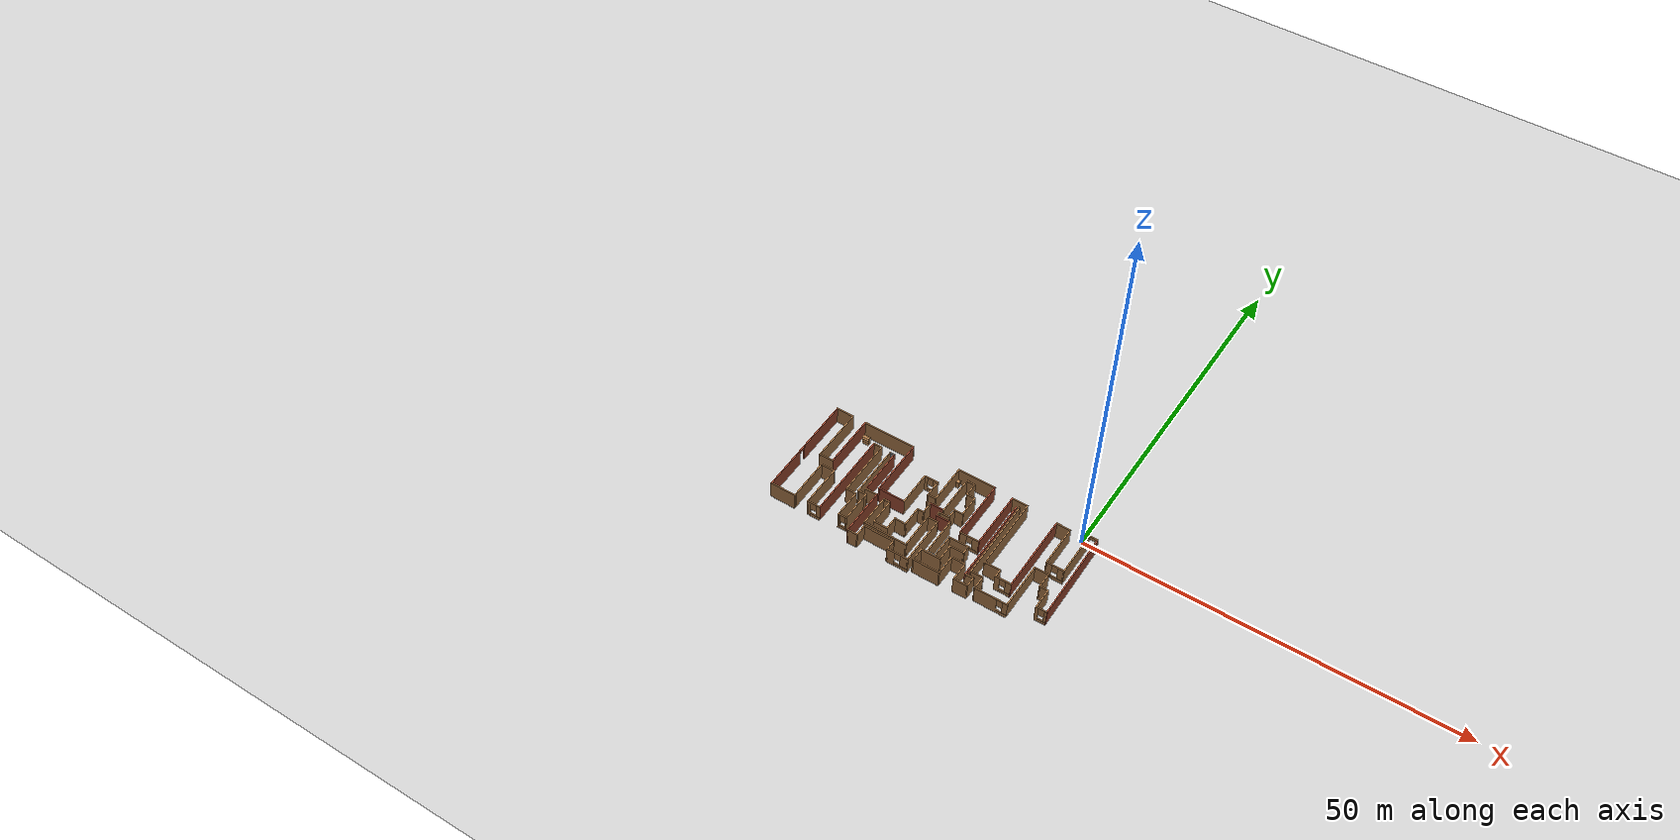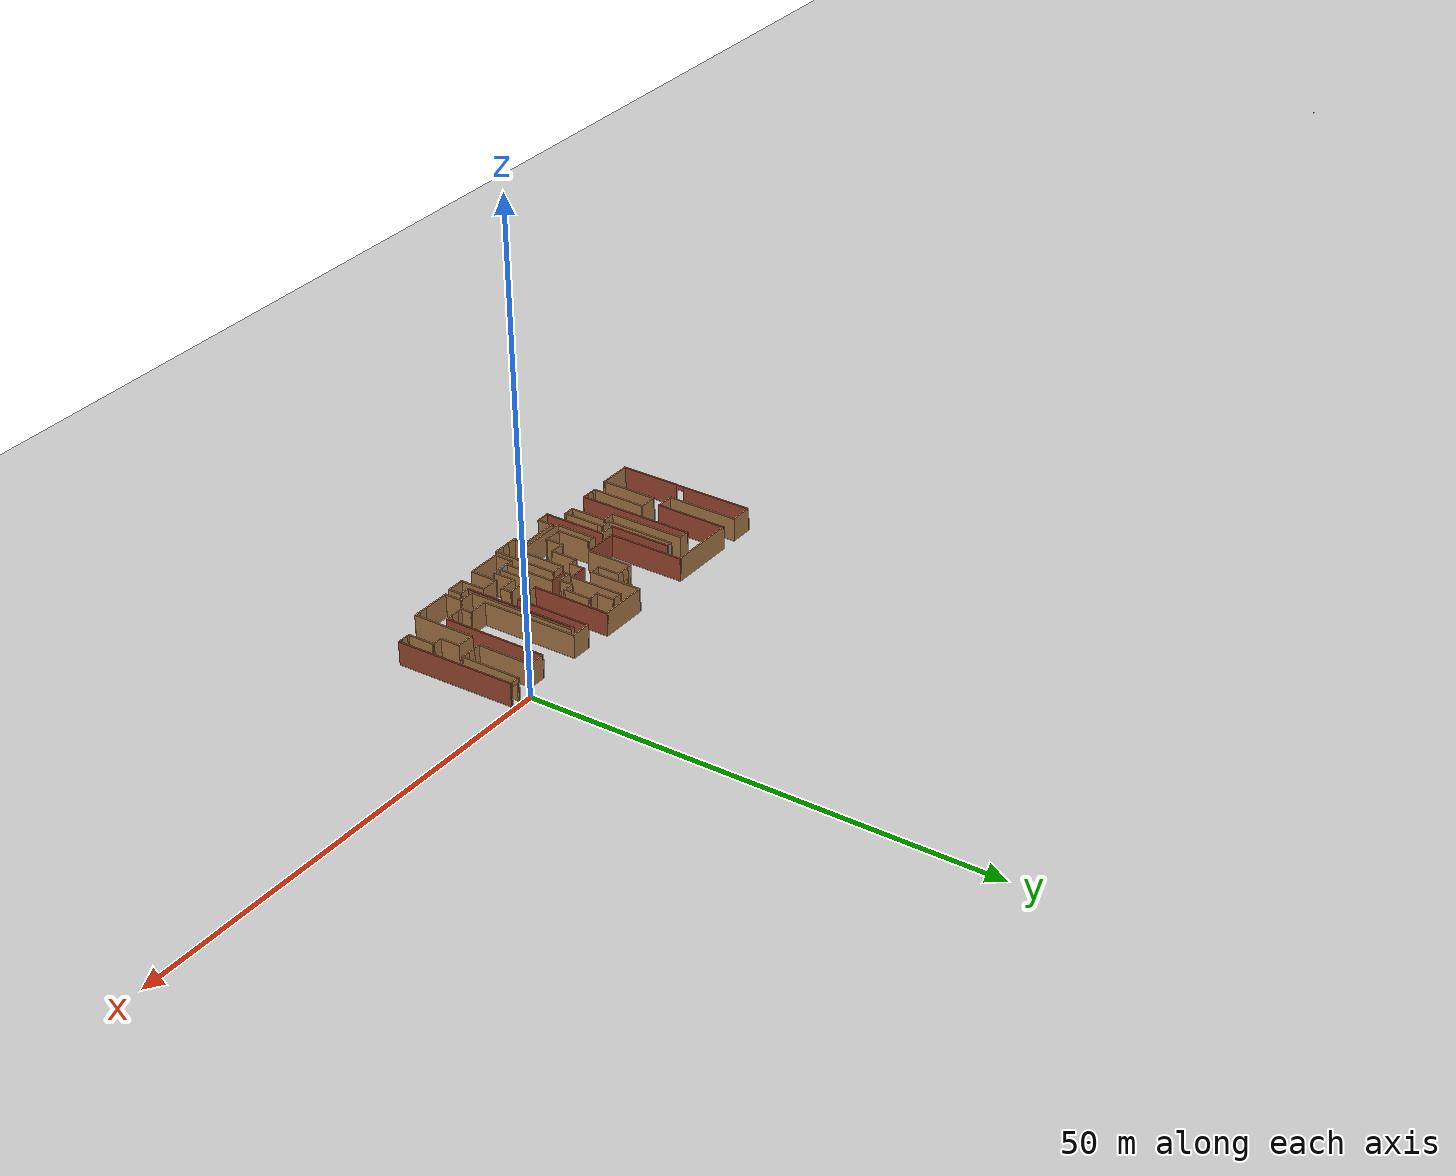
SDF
<sdf version="1.7">
 <world name="default">
  <light name="sun" type="directional">
   <pose>0 0 10 0 -0 0</pose>
   <diffuse>0.8 0.8 0.8 1</diffuse>
   <specular>0.2 0.2 0.2 1</specular>
   <attenuation>
    <range>1000</range>
    <constant>0.9</constant>
    <linear>0.01</linear>
    <quadratic>0.001</quadratic>
   </attenuation>
   <direction>-0.5 0.1 -0.9</direction>
   <spot><inner_angle>0</inner_angle><outer_angle>0</outer_angle><falloff>0</falloff></spot>
  </light>
  <model name="ground_plane">
   <static>1</static>
   <link name="link">
    <collision name="collision">
     <geometry><plane><normal>0 0 1</normal><size>100 100</size></plane></geometry>
     <surface><friction><ode><mu>100</mu><mu2>50</mu2></ode></friction></surface>
    </collision>
    <visual name="visual">
     <cast_shadows>0</cast_shadows>
     <geometry><plane><normal>0 0 1</normal><size>100 100</size></plane></geometry>
     <material>
      <script><uri>file://media/materials/scripts/gazebo.material</uri><name>Gazebo/Grey</name></script>
     </material>
    </visual>
   </link>
  </model>
  <gravity>0 0 -9.8</gravity>
  <magnetic_field>6e-06 2.3e-05 -4.2e-05</magnetic_field>
  <atmosphere type="adiabatic"/>
  <physics type="ode">
   <max_step_size>0.001</max_step_size>
   <real_time_factor>1</real_time_factor>
   <real_time_update_rate>1000</real_time_update_rate>
  </physics>
  <scene><ambient>0.4 0.4 0.4 1</ambient><background>0.7 0.7 0.7 1</background><shadows>1</shadows></scene>
  <audio><device>default</device></audio>
  <spherical_coordinates>
   <surface_model>EARTH_WGS84</surface_model>
   <latitude_deg>0</latitude_deg>
   <longitude_deg>0</longitude_deg>
   <elevation>0</elevation>
   <heading_deg>0</heading_deg>
  </spherical_coordinates>
  <model name="simple_maze">
   <pose>-16.3821 -8.2673 0 0 -0 0</pose>
   <link name="Wall_10">
    <pose>-18.6448 0.41237 0 0 -0 -1.5708</pose>
    <visual name="Wall_10_Visual_0">
     <pose>-3.63677 0 1.25 0 -0 0</pose>
     <geometry><box><size>7.72647 0.15 2.5</size></box></geometry>
     <material>
      <script><uri>file://media/materials/scripts/gazebo.material</uri><name>Gazebo/Bricks</name></script>
      <ambient>1 1 1 1</ambient>
     </material>
     <meta><layer>0</layer></meta>
    </visual>
    <collision name="Wall_10_Collision_0">
     <geometry><box><size>7.72647 0.15 2.5</size></box></geometry>
     <pose>-3.63677 0 1.25 0 -0 0</pose>
    </collision>
    <visual name="Wall_10_Visual_1">
     <pose>4.31323 0 1.25 0 -0 0</pose>
     <geometry><box><size>6.37353 0.15 2.5</size></box></geometry>
     <material>
      <script><uri>file://media/materials/scripts/gazebo.material</uri><name>Gazebo/Bricks</name></script>
      <ambient>1 1 1 1</ambient>
     </material>
     <meta><layer>0</layer></meta>
    </visual>
    <collision name="Wall_10_Collision_1">
     <geometry><box><size>6.37353 0.15 2.5</size></box></geometry>
     <pose>4.31323 0 1.25 0 -0 0</pose>
    </collision>
    <visual name="Wall_10_Visual_2">
     <pose>0.676471 0 2.25 0 -0 0</pose>
     <geometry><box><size>0.9 0.15 0.5</size></box></geometry>
     <material>
      <script><uri>file://media/materials/scripts/gazebo.material</uri><name>Gazebo/Bricks</name></script>
      <ambient>1 1 1 1</ambient>
     </material>
     <meta><layer>0</layer></meta>
    </visual>
    <collision name="Wall_10_Collision_2">
     <geometry><box><size>0.9 0.15 0.5</size></box></geometry>
     <pose>0.676471 0 2.25 0 -0 0</pose>
    </collision>
   </link>
   <link name="Wall_100">
    <collision name="Wall_100_Collision">
     <geometry><box><size>1.25 0.15 2.5</size></box></geometry>
     <pose>0 0 1.25 0 -0 0</pose>
    </collision>
    <visual name="Wall_100_Visual">
     <pose>0 0 1.25 0 -0 0</pose>
     <geometry><box><size>1.25 0.15 2.5</size></box></geometry>
     <material>
      <script><uri>file://media/materials/scripts/gazebo.material</uri><name>Gazebo/Wood</name></script>
      <ambient>1 1 1 1</ambient>
     </material>
     <meta><layer>0</layer></meta>
    </visual>
    <pose>2.5834 2.04227 0 0 -0 3.14159</pose>
   </link>
   <link name="Wall_101">
    <collision name="Wall_101_Collision">
     <geometry><box><size>1.5 0.15 2.5</size></box></geometry>
     <pose>0 0 1.25 0 -0 0</pose>
    </collision>
    <visual name="Wall_101_Visual">
     <pose>0 0 1.25 0 -0 0</pose>
     <geometry><box><size>1.5 0.15 2.5</size></box></geometry>
     <material>
      <script><uri>file://media/materials/scripts/gazebo.material</uri><name>Gazebo/Wood</name></script>
      <ambient>1 1 1 1</ambient>
     </material>
     <meta><layer>0</layer></meta>
    </visual>
    <pose>2.0334 1.36727 0 0 -0 -1.5708</pose>
   </link>
   <link name="Wall_102">
    <collision name="Wall_102_Collision">
     <geometry><box><size>1.5 0.15 2.5</size></box></geometry>
     <pose>0 0 1.25 0 -0 0</pose>
    </collision>
    <visual name="Wall_102_Visual">
     <pose>0 0 1.25 0 -0 0</pose>
     <geometry><box><size>1.5 0.15 2.5</size></box></geometry>
     <material>
      <script><uri>file://media/materials/scripts/gazebo.material</uri><name>Gazebo/Wood</name></script>
      <ambient>1 1 1 1</ambient>
     </material>
     <meta><layer>0</layer></meta>
    </visual>
    <pose>1.3584 0.692271 0 0 -0 3.14159</pose>
   </link>
   <link name="Wall_103">
    <collision name="Wall_103_Collision">
     <geometry><box><size>0.75 0.15 2.5</size></box></geometry>
     <pose>0 0 1.25 0 -0 0</pose>
    </collision>
    <visual name="Wall_103_Visual">
     <pose>0 0 1.25 0 -0 0</pose>
     <geometry><box><size>0.75 0.15 2.5</size></box></geometry>
     <material>
      <script><uri>file://media/materials/scripts/gazebo.material</uri><name>Gazebo/Wood</name></script>
      <ambient>1 1 1 1</ambient>
     </material>
     <meta><layer>0</layer></meta>
    </visual>
    <pose>0.683398 0.392271 0 0 -0 -1.5708</pose>
   </link>
   <link name="Wall_104">
    <collision name="Wall_104_Collision">
     <geometry><box><size>2 0.15 2.5</size></box></geometry>
     <pose>0 0 1.25 0 -0 0</pose>
    </collision>
    <visual name="Wall_104_Visual">
     <pose>0 0 1.25 0 -0 0</pose>
     <geometry><box><size>2 0.15 2.5</size></box></geometry>
     <material>
      <script><uri>file://media/materials/scripts/gazebo.material</uri><name>Gazebo/Bricks</name></script>
      <ambient>1 1 1 1</ambient>
     </material>
     <meta><layer>0</layer></meta>
    </visual>
    <pose>1.6084 0.092271 0 0 -0 0</pose>
   </link>
   <link name="Wall_105">
    <collision name="Wall_105_Collision">
     <geometry><box><size>5.5 0.15 2.5</size></box></geometry>
     <pose>0 0 1.25 0 -0 0</pose>
    </collision>
    <visual name="Wall_105_Visual">
     <pose>0 0 1.25 0 -0 0</pose>
     <geometry><box><size>5.5 0.15 2.5</size></box></geometry>
     <material>
      <script><uri>file://media/materials/scripts/gazebo.material</uri><name>Gazebo/Wood</name></script>
      <ambient>1 1 1 1</ambient>
     </material>
     <meta><layer>0</layer></meta>
    </visual>
    <pose>2.5334 -2.58273 0 0 -0 -1.5708</pose>
   </link>
   <link name="Wall_106">
    <collision name="Wall_106_Collision">
     <geometry><box><size>1.25 0.15 2.5</size></box></geometry>
     <pose>0 0 1.25 0 -0 0</pose>
    </collision>
    <visual name="Wall_106_Visual">
     <pose>0 0 1.25 0 -0 0</pose>
     <geometry><box><size>1.25 0.15 2.5</size></box></geometry>
     <material>
      <script><uri>file://media/materials/scripts/gazebo.material</uri><name>Gazebo/Grey</name></script>
      <ambient>1 1 1 1</ambient>
     </material>
     <meta><layer>0</layer></meta>
    </visual>
    <pose>3.0834 -5.25773 0 0 -0 0</pose>
   </link>
   <link name="Wall_107">
    <collision name="Wall_107_Collision">
     <geometry><box><size>3.5 0.15 2.5</size></box></geometry>
     <pose>0 0 1.25 0 -0 0</pose>
    </collision>
    <visual name="Wall_107_Visual">
     <pose>0 0 1.25 0 -0 0</pose>
     <geometry><box><size>3.5 0.15 2.5</size></box></geometry>
     <material>
      <script><uri>file://media/materials/scripts/gazebo.material</uri><name>Gazebo/Wood</name></script>
      <ambient>1 1 1 1</ambient>
     </material>
     <meta><layer>0</layer></meta>
    </visual>
    <pose>3.6334 -3.58273 0 0 -0 1.5708</pose>
   </link>
   <link name="Wall_108">
    <collision name="Wall_108_Collision">
     <geometry><box><size>2.75 0.15 2.5</size></box></geometry>
     <pose>0 0 1.25 0 -0 0</pose>
    </collision>
    <visual name="Wall_108_Visual">
     <pose>0 0 1.25 0 -0 0</pose>
     <geometry><box><size>2.75 0.15 2.5</size></box></geometry>
     <material>
      <script><uri>file://media/materials/scripts/gazebo.material</uri><name>Gazebo/Wood</name></script>
      <ambient>1 1 1 1</ambient>
     </material>
     <meta><layer>0</layer></meta>
    </visual>
    <pose>4.9334 -1.90773 0 0 -0 0</pose>
   </link>
   <link name="Wall_109">
    <collision name="Wall_109_Collision">
     <geometry><box><size>1.25 0.15 2.5</size></box></geometry>
     <pose>0 0 1.25 0 -0 0</pose>
    </collision>
    <visual name="Wall_109_Visual">
     <pose>0 0 1.25 0 -0 0</pose>
     <geometry><box><size>1.25 0.15 2.5</size></box></geometry>
     <material>
      <script><uri>file://media/materials/scripts/gazebo.material</uri><name>Gazebo/Wood</name></script>
      <ambient>1 1 1 1</ambient>
     </material>
     <meta><layer>0</layer></meta>
    </visual>
    <pose>6.2334 -2.45773 0 0 -0 -1.5708</pose>
   </link>
   <link name="Wall_11">
    <collision name="Wall_11_Collision">
     <geometry><box><size>3.58973 0.15 2.5</size></box></geometry>
     <pose>0 0 1.25 0 -0 0</pose>
    </collision>
    <visual name="Wall_11_Visual">
     <pose>0 0 1.25 0 -0 0</pose>
     <geometry><box><size>3.58973 0.15 2.5</size></box></geometry>
     <material>
      <script><uri>file://media/materials/scripts/gazebo.material</uri><name>Gazebo/Wood</name></script>
      <ambient>1 1 1 1</ambient>
     </material>
     <meta><layer>0</layer></meta>
    </visual>
    <pose>-16.925 -7.01263 0 0 -0 0</pose>
   </link>
   <link name="Wall_110">
    <collision name="Wall_110_Collision">
     <geometry><box><size>2 0.15 2.5</size></box></geometry>
     <pose>0 0 1.25 0 -0 0</pose>
    </collision>
    <visual name="Wall_110_Visual">
     <pose>0 0 1.25 0 -0 0</pose>
     <geometry><box><size>2 0.15 2.5</size></box></geometry>
     <material>
      <script><uri>file://media/materials/scripts/gazebo.material</uri><name>Gazebo/Wood</name></script>
      <ambient>1 1 1 1</ambient>
     </material>
     <meta><layer>0</layer></meta>
    </visual>
    <pose>5.3084 -3.00773 0 0 -0 3.14159</pose>
   </link>
   <link name="Wall_111">
    <collision name="Wall_111_Collision">
     <geometry><box><size>2.5 0.15 2.5</size></box></geometry>
     <pose>0 0 1.25 0 -0 0</pose>
    </collision>
    <visual name="Wall_111_Visual">
     <pose>0 0 1.25 0 -0 0</pose>
     <geometry><box><size>2.5 0.15 2.5</size></box></geometry>
     <material>
      <script><uri>file://media/materials/scripts/gazebo.material</uri><name>Gazebo/Wood</name></script>
      <ambient>1 1 1 1</ambient>
     </material>
     <meta><layer>0</layer></meta>
    </visual>
    <pose>4.3834 -4.18273 0 0 -0 -1.5708</pose>
   </link>
   <link name="Wall_112">
    <collision name="Wall_112_Collision">
     <geometry><box><size>2.75 0.15 2.5</size></box></geometry>
     <pose>0 0 1.25 0 -0 0</pose>
    </collision>
    <visual name="Wall_112_Visual">
     <pose>0 0 1.25 0 -0 0</pose>
     <geometry><box><size>2.75 0.15 2.5</size></box></geometry>
     <material>
      <script><uri>file://media/materials/scripts/gazebo.material</uri><name>Gazebo/Wood</name></script>
      <ambient>1 1 1 1</ambient>
     </material>
     <meta><layer>0</layer></meta>
    </visual>
    <pose>3.0834 -5.35773 0 0 -0 3.14159</pose>
   </link>
   <link name="Wall_113">
    <collision name="Wall_113_Collision">
     <geometry><box><size>2 0.15 2.5</size></box></geometry>
     <pose>0 0 1.25 0 -0 0</pose>
    </collision>
    <visual name="Wall_113_Visual">
     <pose>0 0 1.25 0 -0 0</pose>
     <geometry><box><size>2 0.15 2.5</size></box></geometry>
     <material>
      <script><uri>file://media/materials/scripts/gazebo.material</uri><name>Gazebo/Wood</name></script>
      <ambient>1 1 1 1</ambient>
     </material>
     <meta><layer>0</layer></meta>
    </visual>
    <pose>1.7834 -6.28273 0 0 -0 -1.5708</pose>
   </link>
   <link name="Wall_114">
    <collision name="Wall_114_Collision">
     <geometry><box><size>3.75 0.15 2.5</size></box></geometry>
     <pose>0 0 1.25 0 -0 0</pose>
    </collision>
    <visual name="Wall_114_Visual">
     <pose>0 0 1.25 0 -0 0</pose>
     <geometry><box><size>3.75 0.15 2.5</size></box></geometry>
     <material>
      <script><uri>file://media/materials/scripts/gazebo.material</uri><name>Gazebo/Wood</name></script>
      <ambient>1 1 1 1</ambient>
     </material>
     <meta><layer>0</layer></meta>
    </visual>
    <pose>3.5834 -7.20773 0 0 -0 0</pose>
   </link>
   <link name="Wall_115">
    <collision name="Wall_115_Collision">
     <geometry><box><size>3 0.15 2.5</size></box></geometry>
     <pose>0 0 1.25 0 -0 0</pose>
    </collision>
    <visual name="Wall_115_Visual">
     <pose>0 0 1.25 0 -0 0</pose>
     <geometry><box><size>3 0.15 2.5</size></box></geometry>
     <material>
      <script><uri>file://media/materials/scripts/gazebo.material</uri><name>Gazebo/Wood</name></script>
      <ambient>1 1 1 1</ambient>
     </material>
     <meta><layer>0</layer></meta>
    </visual>
    <pose>5.3834 -5.78273 0 0 -0 1.5708</pose>
   </link>
   <link name="Wall_116">
    <collision name="Wall_116_Collision">
     <geometry><box><size>2 0.15 2.5</size></box></geometry>
     <pose>0 0 1.25 0 -0 0</pose>
    </collision>
    <visual name="Wall_116_Visual">
     <pose>0 0 1.25 0 -0 0</pose>
     <geometry><box><size>2 0.15 2.5</size></box></geometry>
     <material>
      <script><uri>file://media/materials/scripts/gazebo.material</uri><name>Gazebo/Wood</name></script>
      <ambient>1 1 1 1</ambient>
     </material>
     <meta><layer>0</layer></meta>
    </visual>
    <pose>6.3084 -4.35773 0 0 -0 0</pose>
   </link>
   <link name="Wall_117">
    <collision name="Wall_117_Collision">
     <geometry><box><size>2.75 0.15 2.5</size></box></geometry>
     <pose>0 0 1.25 0 -0 0</pose>
    </collision>
    <visual name="Wall_117_Visual">
     <pose>0 0 1.25 0 -0 0</pose>
     <geometry><box><size>2.75 0.15 2.5</size></box></geometry>
     <material>
      <script><uri>file://media/materials/scripts/gazebo.material</uri><name>Gazebo/Wood</name></script>
      <ambient>1 1 1 1</ambient>
     </material>
     <meta><layer>0</layer></meta>
    </visual>
    <pose>7.2334 -5.65773 0 0 -0 -1.5708</pose>
   </link>
   <link name="Wall_118">
    <collision name="Wall_118_Collision">
     <geometry><box><size>2 0.15 2.5</size></box></geometry>
     <pose>0 0 1.25 0 -0 0</pose>
    </collision>
    <visual name="Wall_118_Visual">
     <pose>0 0 1.25 0 -0 0</pose>
     <geometry><box><size>2 0.15 2.5</size></box></geometry>
     <material>
      <script><uri>file://media/materials/scripts/gazebo.material</uri><name>Gazebo/Wood</name></script>
      <ambient>1 1 1 1</ambient>
     </material>
     <meta><layer>0</layer></meta>
    </visual>
    <pose>8.1584 -6.95773 0 0 -0 0</pose>
   </link>
   <link name="Wall_119">
    <collision name="Wall_119_Collision">
     <geometry><box><size>1.5 0.15 2.5</size></box></geometry>
     <pose>0 0 1.25 0 -0 0</pose>
    </collision>
    <visual name="Wall_119_Visual">
     <pose>0 0 1.25 0 -0 0</pose>
     <geometry><box><size>1.5 0.15 2.5</size></box></geometry>
     <material>
      <script><uri>file://media/materials/scripts/gazebo.material</uri><name>Gazebo/Wood</name></script>
      <ambient>1 1 1 1</ambient>
     </material>
     <meta><layer>0</layer></meta>
    </visual>
    <pose>9.0834 -6.28273 0 0 -0 1.5708</pose>
   </link>
   <link name="Wall_12">
    <collision name="Wall_12_Collision">
     <geometry><box><size>6.1172 0.15 2.5</size></box></geometry>
     <pose>0 0 1.25 0 -0 0</pose>
    </collision>
    <visual name="Wall_12_Visual">
     <pose>0 0 1.25 0 -0 0</pose>
     <geometry><box><size>6.1172 0.15 2.5</size></box></geometry>
     <material>
      <script><uri>file://media/materials/scripts/gazebo.material</uri><name>Gazebo/Wood</name></script>
      <ambient>1 1 1 1</ambient>
     </material>
     <meta><layer>0</layer></meta>
    </visual>
    <pose>-15.2357 -4.02903 0 0 -0 1.5708</pose>
   </link>
   <link name="Wall_120">
    <collision name="Wall_120_Collision">
     <geometry><box><size>1.25 0.15 2.5</size></box></geometry>
     <pose>0 0 1.25 0 -0 0</pose>
    </collision>
    <visual name="Wall_120_Visual">
     <pose>0 0 1.25 0 -0 0</pose>
     <geometry><box><size>1.25 0.15 2.5</size></box></geometry>
     <material>
      <script><uri>file://media/materials/scripts/gazebo.material</uri><name>Gazebo/Wood</name></script>
      <ambient>1 1 1 1</ambient>
     </material>
     <meta><layer>0</layer></meta>
    </visual>
    <pose>8.5334 -5.60773 0 0 -0 3.14159</pose>
   </link>
   <link name="Wall_121">
    <collision name="Wall_121_Collision">
     <geometry><box><size>12.5 0.15 2.5</size></box></geometry>
     <pose>0 0 1.25 0 -0 0</pose>
    </collision>
    <visual name="Wall_121_Visual">
     <pose>0 0 1.25 0 -0 0</pose>
     <geometry><box><size>12.5 0.15 2.5</size></box></geometry>
     <material>
      <script><uri>file://media/materials/scripts/gazebo.material</uri><name>Gazebo/Bricks</name></script>
      <ambient>1 1 1 1</ambient>
     </material>
     <meta><layer>0</layer></meta>
    </visual>
    <pose>7.9834 0.567271 0 0 -0 1.5708</pose>
   </link>
   <link name="Wall_122">
    <collision name="Wall_122_Collision">
     <geometry><box><size>0.5 0.15 2.5</size></box></geometry>
     <pose>0 0 1.25 0 -0 0</pose>
    </collision>
    <visual name="Wall_122_Visual">
     <pose>0 0 1.25 0 -0 0</pose>
     <geometry><box><size>0.5 0.15 2.5</size></box></geometry>
     <material>
      <script><uri>file://media/materials/scripts/gazebo.material</uri><name>Gazebo/Wood</name></script>
      <ambient>1 1 1 1</ambient>
     </material>
     <meta><layer>0</layer></meta>
    </visual>
    <pose>8.1584 6.74227 0 0 -0 0</pose>
   </link>
   <link name="Wall_123">
    <collision name="Wall_123_Collision">
     <geometry><box><size>11.75 0.15 2.5</size></box></geometry>
     <pose>0 0 1.25 0 -0 0</pose>
    </collision>
    <visual name="Wall_123_Visual">
     <pose>0 0 1.25 0 -0 0</pose>
     <geometry><box><size>11.75 0.15 2.5</size></box></geometry>
     <material>
      <script><uri>file://media/materials/scripts/gazebo.material</uri><name>Gazebo/Wood</name></script>
      <ambient>1 1 1 1</ambient>
     </material>
     <meta><layer>0</layer></meta>
    </visual>
    <pose>8.3334 0.942271 0 0 -0 -1.5708</pose>
   </link>
   <link name="Wall_124">
    <collision name="Wall_124_Collision">
     <geometry><box><size>1.75 0.15 2.5</size></box></geometry>
     <pose>0 0 1.25 0 -0 0</pose>
    </collision>
    <visual name="Wall_124_Visual">
     <pose>0 0 1.25 0 -0 0</pose>
     <geometry><box><size>1.75 0.15 2.5</size></box></geometry>
     <material>
      <script><uri>file://media/materials/scripts/gazebo.material</uri><name>Gazebo/Wood</name></script>
      <ambient>1 1 1 1</ambient>
     </material>
     <meta><layer>0</layer></meta>
    </visual>
    <pose>9.1334 -4.85773 0 0 -0 0</pose>
   </link>
   <link name="Wall_125">
    <collision name="Wall_125_Collision">
     <geometry><box><size>2 0.15 2.5</size></box></geometry>
     <pose>0 0 1.25 0 -0 0</pose>
    </collision>
    <visual name="Wall_125_Visual">
     <pose>0 0 1.25 0 -0 0</pose>
     <geometry><box><size>2 0.15 2.5</size></box></geometry>
     <material>
      <script><uri>file://media/materials/scripts/gazebo.material</uri><name>Gazebo/Wood</name></script>
      <ambient>1 1 1 1</ambient>
     </material>
     <meta><layer>0</layer></meta>
    </visual>
    <pose>9.9334 -5.78273 0 0 -0 -1.5708</pose>
   </link>
   <link name="Wall_126">
    <pose>12.1084 -6.70773 0 0 -0 0</pose>
    <visual name="Wall_126_Visual_0">
     <pose>-0.728212 0 1.25 0 -0 0</pose>
     <geometry><box><size>3.04358 0.15 2.5</size></box></geometry>
     <material>
      <script><uri>file://media/materials/scripts/gazebo.material</uri><name>Gazebo/Wood</name></script>
      <ambient>1 1 1 1</ambient>
     </material>
     <meta><layer>0</layer></meta>
    </visual>
    <collision name="Wall_126_Collision_0">
     <geometry><box><size>3.04358 0.15 2.5</size></box></geometry>
     <pose>-0.728212 0 1.25 0 -0 0</pose>
    </collision>
    <visual name="Wall_126_Visual_1">
     <pose>1.52179 0 0.25 0 -0 0</pose>
     <geometry><box><size>1.45642 0.15 0.5</size></box></geometry>
     <material>
      <script><uri>file://media/materials/scripts/gazebo.material</uri><name>Gazebo/Wood</name></script>
      <ambient>1 1 1 1</ambient>
     </material>
     <meta><layer>0</layer></meta>
    </visual>
    <collision name="Wall_126_Collision_1">
     <geometry><box><size>1.45642 0.15 0.5</size></box></geometry>
     <pose>1.52179 0 0.25 0 -0 0</pose>
    </collision>
    <visual name="Wall_126_Visual_2">
     <pose>1.92179 0 1.5 0 -0 0</pose>
     <geometry><box><size>0.656423 0.15 2</size></box></geometry>
     <material>
      <script><uri>file://media/materials/scripts/gazebo.material</uri><name>Gazebo/Wood</name></script>
      <ambient>1 1 1 1</ambient>
     </material>
     <meta><layer>0</layer></meta>
    </visual>
    <collision name="Wall_126_Collision_2">
     <geometry><box><size>0.656423 0.15 2</size></box></geometry>
     <pose>1.92179 0 1.5 0 -0 0</pose>
    </collision>
    <visual name="Wall_126_Visual_3">
     <pose>1.19358 0 1.9 0 -0 0</pose>
     <geometry><box><size>0.8 0.15 1.2</size></box></geometry>
     <material>
      <script><uri>file://media/materials/scripts/gazebo.material</uri><name>Gazebo/Wood</name></script>
      <ambient>1 1 1 1</ambient>
     </material>
     <meta><layer>0</layer></meta>
    </visual>
    <collision name="Wall_126_Collision_3">
     <geometry><box><size>0.8 0.15 1.2</size></box></geometry>
     <pose>1.19358 0 1.9 0 -0 0</pose>
    </collision>
   </link>
   <link name="Wall_127">
    <collision name="Wall_127_Collision">
     <geometry><box><size>6.75 0.15 2.5</size></box></geometry>
     <pose>0 0 1.25 0 -0 0</pose>
    </collision>
    <visual name="Wall_127_Visual">
     <pose>0 0 1.25 0 -0 0</pose>
     <geometry><box><size>6.75 0.15 2.5</size></box></geometry>
     <material>
      <script><uri>file://media/materials/scripts/gazebo.material</uri><name>Gazebo/Wood</name></script>
      <ambient>1 1 1 1</ambient>
     </material>
     <meta><layer>0</layer></meta>
    </visual>
    <pose>14.2834 -3.40773 0 0 -0 1.5708</pose>
   </link>
   <link name="Wall_128">
    <collision name="Wall_128_Collision">
     <geometry><box><size>2 0.15 2.5</size></box></geometry>
     <pose>0 0 1.25 0 -0 0</pose>
    </collision>
    <visual name="Wall_128_Visual">
     <pose>0 0 1.25 0 -0 0</pose>
     <geometry><box><size>2 0.15 2.5</size></box></geometry>
     <material>
      <script><uri>file://media/materials/scripts/gazebo.material</uri><name>Gazebo/Wood</name></script>
      <ambient>1 1 1 1</ambient>
     </material>
     <meta><layer>0</layer></meta>
    </visual>
    <pose>15.2084 -0.107729 0 0 -0 0</pose>
   </link>
   <link name="Wall_129">
    <collision name="Wall_129_Collision">
     <geometry><box><size>2.25 0.15 2.5</size></box></geometry>
     <pose>0 0 1.25 0 -0 0</pose>
    </collision>
    <visual name="Wall_129_Visual">
     <pose>0 0 1.25 0 -0 0</pose>
     <geometry><box><size>2.25 0.15 2.5</size></box></geometry>
     <material>
      <script><uri>file://media/materials/scripts/gazebo.material</uri><name>Gazebo/Wood</name></script>
      <ambient>1 1 1 1</ambient>
     </material>
     <meta><layer>0</layer></meta>
    </visual>
    <pose>16.1334 -1.15773 0 0 -0 -1.5708</pose>
   </link>
   <link name="Wall_132">
    <collision name="Wall_132_Collision">
     <geometry><box><size>1.25 0.15 2.5</size></box></geometry>
     <pose>0 0 1.25 0 -0 0</pose>
    </collision>
    <visual name="Wall_132_Visual">
     <pose>0 0 1.25 0 -0 0</pose>
     <geometry><box><size>1.25 0.15 2.5</size></box></geometry>
     <material>
      <script><uri>file://media/materials/scripts/gazebo.material</uri><name>Gazebo/Wood</name></script>
      <ambient>1 1 1 1</ambient>
     </material>
     <meta><layer>0</layer></meta>
    </visual>
    <pose>16.6834 -2.20773 0 0 -0 0</pose>
   </link>
   <link name="Wall_133">
    <collision name="Wall_133_Collision">
     <geometry><box><size>2.94839 0.15 2.5</size></box></geometry>
     <pose>0 0 1.25 0 -0 0</pose>
    </collision>
    <visual name="Wall_133_Visual">
     <pose>0 0 1.25 0 -0 0</pose>
     <geometry><box><size>2.94839 0.15 2.5</size></box></geometry>
     <material>
      <script><uri>file://media/materials/scripts/gazebo.material</uri><name>Gazebo/Wood</name></script>
      <ambient>1 1 1 1</ambient>
     </material>
     <meta><layer>0</layer></meta>
    </visual>
    <pose>17.2334 -3.60692 0 0 -0 -1.5708</pose>
   </link>
   <link name="Wall_134">
    <pose>17.9084 -5.04129 0 0 -0 0</pose>
    <visual name="Wall_134_Visual_0">
     <pose>-0.552015 0 1.25 0 -0 0</pose>
     <geometry><box><size>0.395969 0.15 2.5</size></box></geometry>
     <material>
      <script><uri>file://media/materials/scripts/gazebo.material</uri><name>Gazebo/Wood</name></script>
      <ambient>1 1 1 1</ambient>
     </material>
     <meta><layer>0</layer></meta>
    </visual>
    <collision name="Wall_134_Collision_0">
     <geometry><box><size>0.395969 0.15 2.5</size></box></geometry>
     <pose>-0.552015 0 1.25 0 -0 0</pose>
    </collision>
    <visual name="Wall_134_Visual_1">
     <pose>0.197985 0 0.25 0 -0 0</pose>
     <geometry><box><size>1.10403 0.15 0.5</size></box></geometry>
     <material>
      <script><uri>file://media/materials/scripts/gazebo.material</uri><name>Gazebo/Wood</name></script>
      <ambient>1 1 1 1</ambient>
     </material>
     <meta><layer>0</layer></meta>
    </visual>
    <collision name="Wall_134_Collision_1">
     <geometry><box><size>1.10403 0.15 0.5</size></box></geometry>
     <pose>0.197985 0 0.25 0 -0 0</pose>
    </collision>
    <visual name="Wall_134_Visual_2">
     <pose>0.597985 0 1.5 0 -0 0</pose>
     <geometry><box><size>0.304031 0.15 2</size></box></geometry>
     <material>
      <script><uri>file://media/materials/scripts/gazebo.material</uri><name>Gazebo/Wood</name></script>
      <ambient>1 1 1 1</ambient>
     </material>
     <meta><layer>0</layer></meta>
    </visual>
    <collision name="Wall_134_Collision_2">
     <geometry><box><size>0.304031 0.15 2</size></box></geometry>
     <pose>0.597985 0 1.5 0 -0 0</pose>
    </collision>
    <visual name="Wall_134_Visual_3">
     <pose>0.045969 0 1.9 0 -0 0</pose>
     <geometry><box><size>0.8 0.15 1.2</size></box></geometry>
     <material>
      <script><uri>file://media/materials/scripts/gazebo.material</uri><name>Gazebo/Wood</name></script>
      <ambient>1 1 1 1</ambient>
     </material>
     <meta><layer>0</layer></meta>
    </visual>
    <collision name="Wall_134_Collision_3">
     <geometry><box><size>0.8 0.15 1.2</size></box></geometry>
     <pose>0.045969 0 1.9 0 -0 0</pose>
    </collision>
   </link>
   <link name="Wall_14">
    <collision name="Wall_14_Collision">
     <geometry><box><size>2 0.15 2.5</size></box></geometry>
     <pose>0 0 1.25 0 -0 0</pose>
    </collision>
    <visual name="Wall_14_Visual">
     <pose>0 0 1.25 0 -0 0</pose>
     <geometry><box><size>2 0.15 2.5</size></box></geometry>
     <material>
      <script><uri>file://media/materials/scripts/gazebo.material</uri><name>Gazebo/Wood</name></script>
      <ambient>1 1 1 1</ambient>
     </material>
     <meta><layer>0</layer></meta>
    </visual>
    <pose>-14.2801 -1.04543 0 0 -0 0</pose>
   </link>
   <link name="Wall_16">
    <collision name="Wall_16_Collision">
     <geometry><box><size>5.97261 0.15 2.5</size></box></geometry>
     <pose>0 0 1.25 0 -0 0</pose>
    </collision>
    <visual name="Wall_16_Visual">
     <pose>0 0 1.25 0 -0 0</pose>
     <geometry><box><size>5.97261 0.15 2.5</size></box></geometry>
     <material>
      <script><uri>file://media/materials/scripts/gazebo.material</uri><name>Gazebo/Wood</name></script>
      <ambient>1 1 1 1</ambient>
     </material>
     <meta><layer>0</layer></meta>
    </visual>
    <pose>-13.401 -3.9567 0 0 -0 -1.57605</pose>
   </link>
   <link name="Wall_17">
    <pose>-12.554 -6.86796 0 0 -0 0</pose>
    <visual name="Wall_17_Visual_0">
     <pose>-0.686423 0 1.25 0 -0 0</pose>
     <geometry><box><size>0.501673 0.15 2.5</size></box></geometry>
     <material>
      <script><uri>file://media/materials/scripts/gazebo.material</uri><name>Gazebo/Wood</name></script>
      <ambient>1 1 1 1</ambient>
     </material>
     <meta><layer>0</layer></meta>
    </visual>
    <collision name="Wall_17_Collision_0">
     <geometry><box><size>0.501673 0.15 2.5</size></box></geometry>
     <pose>-0.686423 0 1.25 0 -0 0</pose>
    </collision>
    <visual name="Wall_17_Visual_1">
     <pose>0.250836 0 0.25 0 -0 0</pose>
     <geometry><box><size>1.37285 0.15 0.5</size></box></geometry>
     <material>
      <script><uri>file://media/materials/scripts/gazebo.material</uri><name>Gazebo/Wood</name></script>
      <ambient>1 1 1 1</ambient>
     </material>
     <meta><layer>0</layer></meta>
    </visual>
    <collision name="Wall_17_Collision_1">
     <geometry><box><size>1.37285 0.15 0.5</size></box></geometry>
     <pose>0.250836 0 0.25 0 -0 0</pose>
    </collision>
    <visual name="Wall_17_Visual_2">
     <pose>0.650836 0 1.5 0 -0 0</pose>
     <geometry><box><size>0.572846 0.15 2</size></box></geometry>
     <material>
      <script><uri>file://media/materials/scripts/gazebo.material</uri><name>Gazebo/Wood</name></script>
      <ambient>1 1 1 1</ambient>
     </material>
     <meta><layer>0</layer></meta>
    </visual>
    <collision name="Wall_17_Collision_2">
     <geometry><box><size>0.572846 0.15 2</size></box></geometry>
     <pose>0.650836 0 1.5 0 -0 0</pose>
    </collision>
    <visual name="Wall_17_Visual_3">
     <pose>-0.035586 0 1.9 0 -0 0</pose>
     <geometry><box><size>0.8 0.15 1.2</size></box></geometry>
     <material>
      <script><uri>file://media/materials/scripts/gazebo.material</uri><name>Gazebo/Wood</name></script>
      <ambient>1 1 1 1</ambient>
     </material>
     <meta><layer>0</layer></meta>
    </visual>
    <collision name="Wall_17_Collision_3">
     <geometry><box><size>0.8 0.15 1.2</size></box></geometry>
     <pose>-0.035586 0 1.9 0 -0 0</pose>
    </collision>
   </link>
   <link name="Wall_18">
    <collision name="Wall_18_Collision">
     <geometry><box><size>12.5 0.15 2.5</size></box></geometry>
     <pose>0 0 1.25 0 -0 0</pose>
    </collision>
    <visual name="Wall_18_Visual">
     <pose>0 0 1.25 0 -0 0</pose>
     <geometry><box><size>12.5 0.15 2.5</size></box></geometry>
     <material>
      <script><uri>file://media/materials/scripts/gazebo.material</uri><name>Gazebo/Bricks</name></script>
      <ambient>1 1 1 1</ambient>
     </material>
     <meta><layer>0</layer></meta>
    </visual>
    <pose>-11.6917 -0.662371 0 0 -0 1.5708</pose>
   </link>
   <link name="Wall_29">
    <collision name="Wall_29_Collision">
     <geometry><box><size>2.5 0.15 2.5</size></box></geometry>
     <pose>0 0 1.25 0 -0 0</pose>
    </collision>
    <visual name="Wall_29_Visual">
     <pose>0 0 1.25 0 -0 0</pose>
     <geometry><box><size>2.5 0.15 2.5</size></box></geometry>
     <material>
      <script><uri>file://media/materials/scripts/gazebo.material</uri><name>Gazebo/Wood</name></script>
      <ambient>1 1 1 1</ambient>
     </material>
     <meta><layer>0</layer></meta>
    </visual>
    <pose>-17.4698 7.83737 0 0 -0 0</pose>
   </link>
   <link name="Wall_30">
    <collision name="Wall_30_Collision">
     <geometry><box><size>7.75 0.15 2.5</size></box></geometry>
     <pose>0 0 1.25 0 -0 0</pose>
    </collision>
    <visual name="Wall_30_Visual">
     <pose>0 0 1.25 0 -0 0</pose>
     <geometry><box><size>7.75 0.15 2.5</size></box></geometry>
     <material>
      <script><uri>file://media/materials/scripts/gazebo.material</uri><name>Gazebo/Wood</name></script>
      <ambient>1 1 1 1</ambient>
     </material>
     <meta><layer>0</layer></meta>
    </visual>
    <pose>-16.2948 4.03737 0 0 -0 -1.5708</pose>
   </link>
   <link name="Wall_31">
    <collision name="Wall_31_Collision">
     <geometry><box><size>2 0.15 2.5</size></box></geometry>
     <pose>0 0 1.25 0 -0 0</pose>
    </collision>
    <visual name="Wall_31_Visual">
     <pose>0 0 1.25 0 -0 0</pose>
     <geometry><box><size>2 0.15 2.5</size></box></geometry>
     <material>
      <script><uri>file://media/materials/scripts/gazebo.material</uri><name>Gazebo/Wood</name></script>
      <ambient>1 1 1 1</ambient>
     </material>
     <meta><layer>0</layer></meta>
    </visual>
    <pose>-15.3698 0.23737 0 0 -0 0</pose>
   </link>
   <link name="Wall_32">
    <collision name="Wall_32_Collision">
     <geometry><box><size>7.75 0.15 2.5</size></box></geometry>
     <pose>0 0 1.25 0 -0 0</pose>
    </collision>
    <visual name="Wall_32_Visual">
     <pose>0 0 1.25 0 -0 0</pose>
     <geometry><box><size>7.75 0.15 2.5</size></box></geometry>
     <material>
      <script><uri>file://media/materials/scripts/gazebo.material</uri><name>Gazebo/Bricks</name></script>
      <ambient>1 1 1 1</ambient>
     </material>
     <meta><layer>0</layer></meta>
    </visual>
    <pose>-14.4448 4.03737 0 0 -0 1.5708</pose>
   </link>
   <link name="Wall_33">
    <collision name="Wall_33_Collision">
     <geometry><box><size>7.25 0.15 2.5</size></box></geometry>
     <pose>0 0 1.25 0 -0 0</pose>
    </collision>
    <visual name="Wall_33_Visual">
     <pose>0 0 1.25 0 -0 0</pose>
     <geometry><box><size>7.25 0.15 2.5</size></box></geometry>
     <material>
      <script><uri>file://media/materials/scripts/gazebo.material</uri><name>Gazebo/Wood</name></script>
      <ambient>1 1 1 1</ambient>
     </material>
     <meta><layer>0</layer></meta>
    </visual>
    <pose>-10.8948 7.83737 0 0 -0 0</pose>
   </link>
   <link name="Wall_34">
    <collision name="Wall_34_Collision">
     <geometry><box><size>8.25 0.15 2.5</size></box></geometry>
     <pose>0 0 1.25 0 -0 0</pose>
    </collision>
    <visual name="Wall_34_Visual">
     <pose>0 0 1.25 0 -0 0</pose>
     <geometry><box><size>8.25 0.15 2.5</size></box></geometry>
     <material>
      <script><uri>file://media/materials/scripts/gazebo.material</uri><name>Gazebo/Bricks</name></script>
      <ambient>1 1 1 1</ambient>
     </material>
     <meta><layer>0</layer></meta>
    </visual>
    <pose>-7.34482 3.78737 0 0 -0 -1.5708</pose>
   </link>
   <link name="Wall_35">
    <collision name="Wall_35_Collision">
     <geometry><box><size>3.75 0.15 2.5</size></box></geometry>
     <pose>0 0 1.25 0 -0 0</pose>
    </collision>
    <visual name="Wall_35_Visual">
     <pose>0 0 1.25 0 -0 0</pose>
     <geometry><box><size>3.75 0.15 2.5</size></box></geometry>
     <material>
      <script><uri>file://media/materials/scripts/gazebo.material</uri><name>Gazebo/Bricks</name></script>
      <ambient>1 1 1 1</ambient>
     </material>
     <meta><layer>0</layer></meta>
    </visual>
    <pose>-5.54482 -0.26263 0 0 -0 0</pose>
   </link>
   <link name="Wall_36">
    <collision name="Wall_36_Collision">
     <geometry><box><size>5 0.15 2.5</size></box></geometry>
     <pose>0 0 1.25 0 -0 0</pose>
    </collision>
    <visual name="Wall_36_Visual">
     <pose>0 0 1.25 0 -0 0</pose>
     <geometry><box><size>5 0.15 2.5</size></box></geometry>
     <material>
      <script><uri>file://media/materials/scripts/gazebo.material</uri><name>Gazebo/Wood</name></script>
      <ambient>1 1 1 1</ambient>
     </material>
     <meta><layer>0</layer></meta>
    </visual>
    <pose>-3.74482 2.16237 0 0 -0 1.5708</pose>
   </link>
   <link name="Wall_37">
    <pose>-2.81982 4.58737 0 0 -0 0</pose>
    <visual name="Wall_37_Visual_0">
     <pose>-0.73022 0 1.25 0 -0 0</pose>
     <geometry><box><size>0.539559 0.15 2.5</size></box></geometry>
     <material>
      <script><uri>file://media/materials/scripts/gazebo.material</uri><name>Gazebo/Wood</name></script>
      <ambient>1 1 1 1</ambient>
     </material>
     <meta><layer>0</layer></meta>
    </visual>
    <collision name="Wall_37_Collision_0">
     <geometry><box><size>0.539559 0.15 2.5</size></box></geometry>
     <pose>-0.73022 0 1.25 0 -0 0</pose>
    </collision>
    <visual name="Wall_37_Visual_1">
     <pose>0.26978 0 0.25 0 -0 0</pose>
     <geometry><box><size>1.46044 0.15 0.5</size></box></geometry>
     <material>
      <script><uri>file://media/materials/scripts/gazebo.material</uri><name>Gazebo/Wood</name></script>
      <ambient>1 1 1 1</ambient>
     </material>
     <meta><layer>0</layer></meta>
    </visual>
    <collision name="Wall_37_Collision_1">
     <geometry><box><size>1.46044 0.15 0.5</size></box></geometry>
     <pose>0.26978 0 0.25 0 -0 0</pose>
    </collision>
    <visual name="Wall_37_Visual_2">
     <pose>0.66978 0 1.5 0 -0 0</pose>
     <geometry><box><size>0.660441 0.15 2</size></box></geometry>
     <material>
      <script><uri>file://media/materials/scripts/gazebo.material</uri><name>Gazebo/Wood</name></script>
      <ambient>1 1 1 1</ambient>
     </material>
     <meta><layer>0</layer></meta>
    </visual>
    <collision name="Wall_37_Collision_2">
     <geometry><box><size>0.660441 0.15 2</size></box></geometry>
     <pose>0.66978 0 1.5 0 -0 0</pose>
    </collision>
    <visual name="Wall_37_Visual_3">
     <pose>-0.060441 0 1.9 0 -0 0</pose>
     <geometry><box><size>0.8 0.15 1.2</size></box></geometry>
     <material>
      <script><uri>file://media/materials/scripts/gazebo.material</uri><name>Gazebo/Wood</name></script>
      <ambient>1 1 1 1</ambient>
     </material>
     <meta><layer>0</layer></meta>
    </visual>
    <collision name="Wall_37_Collision_3">
     <geometry><box><size>0.8 0.15 1.2</size></box></geometry>
     <pose>-0.060441 0 1.9 0 -0 0</pose>
    </collision>
   </link>
   <link name="Wall_38">
    <collision name="Wall_38_Collision">
     <geometry><box><size>2.5 0.15 2.5</size></box></geometry>
     <pose>0 0 1.25 0 -0 0</pose>
    </collision>
    <visual name="Wall_38_Visual">
     <pose>0 0 1.25 0 -0 0</pose>
     <geometry><box><size>2.5 0.15 2.5</size></box></geometry>
     <material>
      <script><uri>file://media/materials/scripts/gazebo.material</uri><name>Gazebo/Wood</name></script>
      <ambient>1 1 1 1</ambient>
     </material>
     <meta><layer>0</layer></meta>
    </visual>
    <pose>-1.89482 3.41237 0 0 -0 -1.5708</pose>
   </link>
   <link name="Wall_39">
    <collision name="Wall_39_Collision">
     <geometry><box><size>1.25 0.15 2.5</size></box></geometry>
     <pose>0 0 1.25 0 -0 0</pose>
    </collision>
    <visual name="Wall_39_Visual">
     <pose>0 0 1.25 0 -0 0</pose>
     <geometry><box><size>1.25 0.15 2.5</size></box></geometry>
     <material>
      <script><uri>file://media/materials/scripts/gazebo.material</uri><name>Gazebo/Wood</name></script>
      <ambient>1 1 1 1</ambient>
     </material>
     <meta><layer>0</layer></meta>
    </visual>
    <pose>-1.34482 2.23737 0 0 -0 0</pose>
   </link>
   <link name="Wall_40">
    <collision name="Wall_40_Collision">
     <geometry><box><size>5.75 0.15 2.5</size></box></geometry>
     <pose>0 0 1.25 0 -0 0</pose>
    </collision>
    <visual name="Wall_40_Visual">
     <pose>0 0 1.25 0 -0 0</pose>
     <geometry><box><size>5.75 0.15 2.5</size></box></geometry>
     <material>
      <script><uri>file://media/materials/scripts/gazebo.material</uri><name>Gazebo/Wood</name></script>
      <ambient>1 1 1 1</ambient>
     </material>
     <meta><layer>0</layer></meta>
    </visual>
    <pose>-0.794816 5.03737 0 0 -0 1.5708</pose>
   </link>
   <link name="Wall_41">
    <collision name="Wall_41_Collision">
     <geometry><box><size>5.25 0.15 2.5</size></box></geometry>
     <pose>0 0 1.25 0 -0 0</pose>
    </collision>
    <visual name="Wall_41_Visual">
     <pose>0 0 1.25 0 -0 0</pose>
     <geometry><box><size>5.25 0.15 2.5</size></box></geometry>
     <material>
      <script><uri>file://media/materials/scripts/gazebo.material</uri><name>Gazebo/Wood</name></script>
      <ambient>1 1 1 1</ambient>
     </material>
     <meta><layer>0</layer></meta>
    </visual>
    <pose>1.75518 7.83737 0 0 -0 0</pose>
   </link>
   <link name="Wall_42">
    <collision name="Wall_42_Collision">
     <geometry><box><size>8.5 0.15 2.5</size></box></geometry>
     <pose>0 0 1.25 0 -0 0</pose>
    </collision>
    <visual name="Wall_42_Visual">
     <pose>0 0 1.25 0 -0 0</pose>
     <geometry><box><size>8.5 0.15 2.5</size></box></geometry>
     <material>
      <script><uri>file://media/materials/scripts/gazebo.material</uri><name>Gazebo/Bricks</name></script>
      <ambient>1 1 1 1</ambient>
     </material>
     <meta><layer>0</layer></meta>
    </visual>
    <pose>4.30518 3.66237 0 0 -0 -1.5708</pose>
   </link>
   <link name="Wall_43">
    <pose>5.60518 -0.51263 0 0 -0 0</pose>
    <visual name="Wall_43_Visual_0">
     <pose>-0.882385 0 1.25 0 -0 0</pose>
     <geometry><box><size>0.985231 0.15 2.5</size></box></geometry>
     <material>
      <script><uri>file://media/materials/scripts/gazebo.material</uri><name>Gazebo/Wood</name></script>
      <ambient>1 1 1 1</ambient>
     </material>
     <meta><layer>0</layer></meta>
    </visual>
    <collision name="Wall_43_Collision_0">
     <geometry><box><size>0.985231 0.15 2.5</size></box></geometry>
     <pose>-0.882385 0 1.25 0 -0 0</pose>
    </collision>
    <visual name="Wall_43_Visual_1">
     <pose>0.492615 0 0.25 0 -0 0</pose>
     <geometry><box><size>1.76477 0.15 0.5</size></box></geometry>
     <material>
      <script><uri>file://media/materials/scripts/gazebo.material</uri><name>Gazebo/Wood</name></script>
      <ambient>1 1 1 1</ambient>
     </material>
     <meta><layer>0</layer></meta>
    </visual>
    <collision name="Wall_43_Collision_1">
     <geometry><box><size>1.76477 0.15 0.5</size></box></geometry>
     <pose>0.492615 0 0.25 0 -0 0</pose>
    </collision>
    <visual name="Wall_43_Visual_2">
     <pose>0.892615 0 1.5 0 -0 0</pose>
     <geometry><box><size>0.964769 0.15 2</size></box></geometry>
     <material>
      <script><uri>file://media/materials/scripts/gazebo.material</uri><name>Gazebo/Wood</name></script>
      <ambient>1 1 1 1</ambient>
     </material>
     <meta><layer>0</layer></meta>
    </visual>
    <collision name="Wall_43_Collision_2">
     <geometry><box><size>0.964769 0.15 2</size></box></geometry>
     <pose>0.892615 0 1.5 0 -0 0</pose>
    </collision>
    <visual name="Wall_43_Visual_3">
     <pose>0.010231 0 1.9 0 -0 0</pose>
     <geometry><box><size>0.8 0.15 1.2</size></box></geometry>
     <material>
      <script><uri>file://media/materials/scripts/gazebo.material</uri><name>Gazebo/Wood</name></script>
      <ambient>1 1 1 1</ambient>
     </material>
     <meta><layer>0</layer></meta>
    </visual>
    <collision name="Wall_43_Collision_3">
     <geometry><box><size>0.8 0.15 1.2</size></box></geometry>
     <pose>0.010231 0 1.9 0 -0 0</pose>
    </collision>
   </link>
   <link name="Wall_44">
    <collision name="Wall_44_Collision">
     <geometry><box><size>8.25 0.15 2.5</size></box></geometry>
     <pose>0 0 1.25 0 -0 0</pose>
    </collision>
    <visual name="Wall_44_Visual">
     <pose>0 0 1.25 0 -0 0</pose>
     <geometry><box><size>8.25 0.15 2.5</size></box></geometry>
     <material>
      <script><uri>file://media/materials/scripts/gazebo.material</uri><name>Gazebo/Bricks</name></script>
      <ambient>1 1 1 1</ambient>
     </material>
     <meta><layer>0</layer></meta>
    </visual>
    <pose>6.90518 3.53737 0 0 -0 1.5708</pose>
   </link>
   <link name="Wall_45">
    <collision name="Wall_45_Collision">
     <geometry><box><size>2.25 0.15 2.5</size></box></geometry>
     <pose>0 0 1.25 0 -0 0</pose>
    </collision>
    <visual name="Wall_45_Visual">
     <pose>0 0 1.25 0 -0 0</pose>
     <geometry><box><size>2.25 0.15 2.5</size></box></geometry>
     <material>
      <script><uri>file://media/materials/scripts/gazebo.material</uri><name>Gazebo/Wood</name></script>
      <ambient>1 1 1 1</ambient>
     </material>
     <meta><layer>0</layer></meta>
    </visual>
    <pose>7.95518 7.58737 0 0 -0 0</pose>
   </link>
   <link name="Wall_46">
    <collision name="Wall_46_Collision">
     <geometry><box><size>10.5 0.15 2.5</size></box></geometry>
     <pose>0 0 1.25 0 -0 0</pose>
    </collision>
    <visual name="Wall_46_Visual">
     <pose>0 0 1.25 0 -0 0</pose>
     <geometry><box><size>10.5 0.15 2.5</size></box></geometry>
     <material>
      <script><uri>file://media/materials/scripts/gazebo.material</uri><name>Gazebo/Wood</name></script>
      <ambient>1 1 1 1</ambient>
     </material>
     <meta><layer>0</layer></meta>
    </visual>
    <pose>9.00518 2.41237 0 0 -0 -1.5708</pose>
   </link>
   <link name="Wall_47">
    <collision name="Wall_47_Collision">
     <geometry><box><size>2.25 0.15 2.5</size></box></geometry>
     <pose>0 0 1.25 0 -0 0</pose>
    </collision>
    <visual name="Wall_47_Visual">
     <pose>0 0 1.25 0 -0 0</pose>
     <geometry><box><size>2.25 0.15 2.5</size></box></geometry>
     <material>
      <script><uri>file://media/materials/scripts/gazebo.material</uri><name>Gazebo/Wood</name></script>
      <ambient>1 1 1 1</ambient>
     </material>
     <meta><layer>0</layer></meta>
    </visual>
    <pose>10.0552 -2.76263 0 0 -0 0</pose>
   </link>
   <link name="Wall_48">
    <collision name="Wall_48_Collision">
     <geometry><box><size>1.25 0.15 2.5</size></box></geometry>
     <pose>0 0 1.25 0 -0 0</pose>
    </collision>
    <visual name="Wall_48_Visual">
     <pose>0 0 1.25 0 -0 0</pose>
     <geometry><box><size>1.25 0.15 2.5</size></box></geometry>
     <material>
      <script><uri>file://media/materials/scripts/gazebo.material</uri><name>Gazebo/Wood</name></script>
      <ambient>1 1 1 1</ambient>
     </material>
     <meta><layer>0</layer></meta>
    </visual>
    <pose>11.1052 -3.31263 0 0 -0 -1.5708</pose>
   </link>
   <link name="Wall_49">
    <pose>12.1552 -3.86263 0 0 -0 0</pose>
    <visual name="Wall_49_Visual_0">
     <pose>-0.795938 0 1.25 0 -0 0</pose>
     <geometry><box><size>0.658124 0.15 2.5</size></box></geometry>
     <material>
      <script><uri>file://media/materials/scripts/gazebo.material</uri><name>Gazebo/Wood</name></script>
      <ambient>1 1 1 1</ambient>
     </material>
     <meta><layer>0</layer></meta>
    </visual>
    <collision name="Wall_49_Collision_0">
     <geometry><box><size>0.658124 0.15 2.5</size></box></geometry>
     <pose>-0.795938 0 1.25 0 -0 0</pose>
    </collision>
    <visual name="Wall_49_Visual_1">
     <pose>0.329062 0 0.25 0 -0 0</pose>
     <geometry><box><size>1.59188 0.15 0.5</size></box></geometry>
     <material>
      <script><uri>file://media/materials/scripts/gazebo.material</uri><name>Gazebo/Wood</name></script>
      <ambient>1 1 1 1</ambient>
     </material>
     <meta><layer>0</layer></meta>
    </visual>
    <collision name="Wall_49_Collision_1">
     <geometry><box><size>1.59188 0.15 0.5</size></box></geometry>
     <pose>0.329062 0 0.25 0 -0 0</pose>
    </collision>
    <visual name="Wall_49_Visual_2">
     <pose>0.729062 0 1.5 0 -0 0</pose>
     <geometry><box><size>0.791876 0.15 2</size></box></geometry>
     <material>
      <script><uri>file://media/materials/scripts/gazebo.material</uri><name>Gazebo/Wood</name></script>
      <ambient>1 1 1 1</ambient>
     </material>
     <meta><layer>0</layer></meta>
    </visual>
    <collision name="Wall_49_Collision_2">
     <geometry><box><size>0.791876 0.15 2</size></box></geometry>
     <pose>0.729062 0 1.5 0 -0 0</pose>
    </collision>
    <visual name="Wall_49_Visual_3">
     <pose>-0.066876 0 1.9 0 -0 0</pose>
     <geometry><box><size>0.8 0.15 1.2</size></box></geometry>
     <material>
      <script><uri>file://media/materials/scripts/gazebo.material</uri><name>Gazebo/Wood</name></script>
      <ambient>1 1 1 1</ambient>
     </material>
     <meta><layer>0</layer></meta>
    </visual>
    <collision name="Wall_49_Collision_3">
     <geometry><box><size>0.8 0.15 1.2</size></box></geometry>
     <pose>-0.066876 0 1.9 0 -0 0</pose>
    </collision>
   </link>
   <link name="Wall_50">
    <collision name="Wall_50_Collision">
     <geometry><box><size>11.25 0.15 2.5</size></box></geometry>
     <pose>0 0 1.25 0 -0 0</pose>
    </collision>
    <visual name="Wall_50_Visual">
     <pose>0 0 1.25 0 -0 0</pose>
     <geometry><box><size>11.25 0.15 2.5</size></box></geometry>
     <material>
      <script><uri>file://media/materials/scripts/gazebo.material</uri><name>Gazebo/Bricks</name></script>
      <ambient>1 1 1 1</ambient>
     </material>
     <meta><layer>0</layer></meta>
    </visual>
    <pose>13.2052 1.68737 0 0 -0 1.5708</pose>
   </link>
   <link name="Wall_51">
    <collision name="Wall_51_Collision">
     <geometry><box><size>2 0.15 2.5</size></box></geometry>
     <pose>0 0 1.25 0 -0 0</pose>
    </collision>
    <visual name="Wall_51_Visual">
     <pose>0 0 1.25 0 -0 0</pose>
     <geometry><box><size>2 0.15 2.5</size></box></geometry>
     <material>
      <script><uri>file://media/materials/scripts/gazebo.material</uri><name>Gazebo/Wood</name></script>
      <ambient>1 1 1 1</ambient>
     </material>
     <meta><layer>0</layer></meta>
    </visual>
    <pose>14.1302 7.23737 0 0 -0 0</pose>
   </link>
   <link name="Wall_52">
    <collision name="Wall_52_Collision">
     <geometry><box><size>6 0.15 2.5</size></box></geometry>
     <pose>0 0 1.25 0 -0 0</pose>
    </collision>
    <visual name="Wall_52_Visual">
     <pose>0 0 1.25 0 -0 0</pose>
     <geometry><box><size>6 0.15 2.5</size></box></geometry>
     <material>
      <script><uri>file://media/materials/scripts/gazebo.material</uri><name>Gazebo/Wood</name></script>
      <ambient>1 1 1 1</ambient>
     </material>
     <meta><layer>0</layer></meta>
    </visual>
    <pose>15.0552 4.31237 0 0 -0 -1.5708</pose>
   </link>
   <link name="Wall_53">
    <pose>16.2302 1.38737 0 0 -0 0</pose>
    <visual name="Wall_53_Visual_0">
     <pose>-0.832704 0 1.25 0 -0 0</pose>
     <geometry><box><size>0.834592 0.15 2.5</size></box></geometry>
     <material>
      <script><uri>file://media/materials/scripts/gazebo.material</uri><name>Gazebo/Wood</name></script>
      <ambient>1 1 1 1</ambient>
     </material>
     <meta><layer>0</layer></meta>
    </visual>
    <collision name="Wall_53_Collision_0">
     <geometry><box><size>0.834592 0.15 2.5</size></box></geometry>
     <pose>-0.832704 0 1.25 0 -0 0</pose>
    </collision>
    <visual name="Wall_53_Visual_1">
     <pose>0.417296 0 0.25 0 -0 0</pose>
     <geometry><box><size>1.66541 0.15 0.5</size></box></geometry>
     <material>
      <script><uri>file://media/materials/scripts/gazebo.material</uri><name>Gazebo/Wood</name></script>
      <ambient>1 1 1 1</ambient>
     </material>
     <meta><layer>0</layer></meta>
    </visual>
    <collision name="Wall_53_Collision_1">
     <geometry><box><size>1.66541 0.15 0.5</size></box></geometry>
     <pose>0.417296 0 0.25 0 -0 0</pose>
    </collision>
    <visual name="Wall_53_Visual_2">
     <pose>0.817296 0 1.5 0 -0 0</pose>
     <geometry><box><size>0.865408 0.15 2</size></box></geometry>
     <material>
      <script><uri>file://media/materials/scripts/gazebo.material</uri><name>Gazebo/Wood</name></script>
      <ambient>1 1 1 1</ambient>
     </material>
     <meta><layer>0</layer></meta>
    </visual>
    <collision name="Wall_53_Collision_2">
     <geometry><box><size>0.865408 0.15 2</size></box></geometry>
     <pose>0.817296 0 1.5 0 -0 0</pose>
    </collision>
    <visual name="Wall_53_Visual_3">
     <pose>-0.015408 0 1.9 0 -0 0</pose>
     <geometry><box><size>0.8 0.15 1.2</size></box></geometry>
     <material>
      <script><uri>file://media/materials/scripts/gazebo.material</uri><name>Gazebo/Wood</name></script>
      <ambient>1 1 1 1</ambient>
     </material>
     <meta><layer>0</layer></meta>
    </visual>
    <collision name="Wall_53_Collision_3">
     <geometry><box><size>0.8 0.15 1.2</size></box></geometry>
     <pose>-0.015408 0 1.9 0 -0 0</pose>
    </collision>
   </link>
   <link name="Wall_54">
    <collision name="Wall_54_Collision">
     <geometry><box><size>6.5 0.15 2.5</size></box></geometry>
     <pose>0 0 1.25 0 -0 0</pose>
    </collision>
    <visual name="Wall_54_Visual">
     <pose>0 0 1.25 0 -0 0</pose>
     <geometry><box><size>6.5 0.15 2.5</size></box></geometry>
     <material>
      <script><uri>file://media/materials/scripts/gazebo.material</uri><name>Gazebo/Wood</name></script>
      <ambient>1 1 1 1</ambient>
     </material>
     <meta><layer>0</layer></meta>
    </visual>
    <pose>17.4052 4.56237 0 0 -0 1.5708</pose>
   </link>
   <link name="Wall_55">
    <pose>17.9552 7.73737 0 0 -0 0</pose>
    <visual name="Wall_55_Visual_0">
     <pose>-0.537909 0 1.25 0 -0 0</pose>
     <geometry><box><size>0.174182 0.15 2.5</size></box></geometry>
     <material>
      <script><uri>file://media/materials/scripts/gazebo.material</uri><name>Gazebo/Wood</name></script>
      <ambient>1 1 1 1</ambient>
     </material>
     <meta><layer>0</layer></meta>
    </visual>
    <collision name="Wall_55_Collision_0">
     <geometry><box><size>0.174182 0.15 2.5</size></box></geometry>
     <pose>-0.537909 0 1.25 0 -0 0</pose>
    </collision>
    <visual name="Wall_55_Visual_1">
     <pose>0.537091 0 1.25 0 -0 0</pose>
     <geometry><box><size>0.175818 0.15 2.5</size></box></geometry>
     <material>
      <script><uri>file://media/materials/scripts/gazebo.material</uri><name>Gazebo/Wood</name></script>
      <ambient>1 1 1 1</ambient>
     </material>
     <meta><layer>0</layer></meta>
    </visual>
    <collision name="Wall_55_Collision_1">
     <geometry><box><size>0.175818 0.15 2.5</size></box></geometry>
     <pose>0.537091 0 1.25 0 -0 0</pose>
    </collision>
    <visual name="Wall_55_Visual_2">
     <pose>-0.000818 0 2.25 0 -0 0</pose>
     <geometry><box><size>0.9 0.15 0.5</size></box></geometry>
     <material>
      <script><uri>file://media/materials/scripts/gazebo.material</uri><name>Gazebo/Wood</name></script>
      <ambient>1 1 1 1</ambient>
     </material>
     <meta><layer>0</layer></meta>
    </visual>
    <collision name="Wall_55_Collision_2">
     <geometry><box><size>0.9 0.15 0.5</size></box></geometry>
     <pose>-0.000818 0 2.25 0 -0 0</pose>
    </collision>
   </link>
   <link name="Wall_57">
    <collision name="Wall_57_Collision">
     <geometry><box><size>1.25 0.15 2.5</size></box></geometry>
     <pose>0 0 1.25 0 -0 0</pose>
    </collision>
    <visual name="Wall_57_Visual">
     <pose>0 0 1.25 0 -0 0</pose>
     <geometry><box><size>1.25 0.15 2.5</size></box></geometry>
     <material>
      <script><uri>file://media/materials/scripts/gazebo.material</uri><name>Gazebo/Wood</name></script>
      <ambient>1 1 1 1</ambient>
     </material>
     <meta><layer>0</layer></meta>
    </visual>
    <pose>-11.1417 5.51263 0 0 -0 0</pose>
   </link>
   <link name="Wall_58">
    <collision name="Wall_58_Collision">
     <geometry><box><size>8.25 0.15 2.5</size></box></geometry>
     <pose>0 0 1.25 0 -0 0</pose>
    </collision>
    <visual name="Wall_58_Visual">
     <pose>0 0 1.25 0 -0 0</pose>
     <geometry><box><size>8.25 0.15 2.5</size></box></geometry>
     <material>
      <script><uri>file://media/materials/scripts/gazebo.material</uri><name>Gazebo/Wood</name></script>
      <ambient>1 1 1 1</ambient>
     </material>
     <meta><layer>0</layer></meta>
    </visual>
    <pose>-10.5917 1.46263 0 0 -0 -1.5708</pose>
   </link>
   <link name="Wall_59">
    <collision name="Wall_59_Collision">
     <geometry><box><size>1.5 0.15 2.5</size></box></geometry>
     <pose>0 0 1.25 0 -0 0</pose>
    </collision>
    <visual name="Wall_59_Visual">
     <pose>0 0 1.25 0 -0 0</pose>
     <geometry><box><size>1.5 0.15 2.5</size></box></geometry>
     <material>
      <script><uri>file://media/materials/scripts/gazebo.material</uri><name>Gazebo/Wood</name></script>
      <ambient>1 1 1 1</ambient>
     </material>
     <meta><layer>0</layer></meta>
    </visual>
    <pose>-9.91675 -2.58737 0 0 -0 0</pose>
   </link>
   <link name="Wall_6">
    <collision name="Wall_6_Collision">
     <geometry><box><size>12.9008 0.15 2.5</size></box></geometry>
     <pose>0 0 1.25 0 -0 0</pose>
    </collision>
    <visual name="Wall_6_Visual">
     <pose>0 0 1.25 0 -0 0</pose>
     <geometry><box><size>12.9008 0.15 2.5</size></box></geometry>
     <material>
      <script><uri>file://media/materials/scripts/gazebo.material</uri><name>Gazebo/Bricks</name></script>
      <ambient>1 1 1 1</ambient>
     </material>
     <meta><layer>0</layer></meta>
    </visual>
    <pose>18.5746 1.36237 0 0 -0 1.58168</pose>
   </link>
   <link name="Wall_60">
    <collision name="Wall_60_Collision">
     <geometry><box><size>4 0.15 2.5</size></box></geometry>
     <pose>0 0 1.25 0 -0 0</pose>
    </collision>
    <visual name="Wall_60_Visual">
     <pose>0 0 1.25 0 -0 0</pose>
     <geometry><box><size>4 0.15 2.5</size></box></geometry>
     <material>
      <script><uri>file://media/materials/scripts/gazebo.material</uri><name>Gazebo/Wood</name></script>
      <ambient>1 1 1 1</ambient>
     </material>
     <meta><layer>0</layer></meta>
    </visual>
    <pose>-9.24175 -4.51237 0 0 -0 -1.5708</pose>
   </link>
   <link name="Wall_61">
    <pose>-8.69175 -6.43737 0 0 -0 0</pose>
    <visual name="Wall_61_Visual_0">
     <pose>-0.499327 0 1.25 0 -0 0</pose>
     <geometry><box><size>0.251345 0.15 2.5</size></box></geometry>
     <material>
      <script><uri>file://media/materials/scripts/gazebo.material</uri><name>Gazebo/Wood</name></script>
      <ambient>1 1 1 1</ambient>
     </material>
     <meta><layer>0</layer></meta>
    </visual>
    <collision name="Wall_61_Collision_0">
     <geometry><box><size>0.251345 0.15 2.5</size></box></geometry>
     <pose>-0.499327 0 1.25 0 -0 0</pose>
    </collision>
    <visual name="Wall_61_Visual_1">
     <pose>0.125673 0 0.25 0 -0 0</pose>
     <geometry><box><size>0.998655 0.15 0.5</size></box></geometry>
     <material>
      <script><uri>file://media/materials/scripts/gazebo.material</uri><name>Gazebo/Wood</name></script>
      <ambient>1 1 1 1</ambient>
     </material>
     <meta><layer>0</layer></meta>
    </visual>
    <collision name="Wall_61_Collision_1">
     <geometry><box><size>0.998655 0.15 0.5</size></box></geometry>
     <pose>0.125673 0 0.25 0 -0 0</pose>
    </collision>
    <visual name="Wall_61_Visual_2">
     <pose>0.525673 0 1.5 0 -0 0</pose>
     <geometry><box><size>0.198655 0.15 2</size></box></geometry>
     <material>
      <script><uri>file://media/materials/scripts/gazebo.material</uri><name>Gazebo/Wood</name></script>
      <ambient>1 1 1 1</ambient>
     </material>
     <meta><layer>0</layer></meta>
    </visual>
    <collision name="Wall_61_Collision_2">
     <geometry><box><size>0.198655 0.15 2</size></box></geometry>
     <pose>0.525673 0 1.5 0 -0 0</pose>
    </collision>
    <visual name="Wall_61_Visual_3">
     <pose>0.026345 0 1.9 0 -0 0</pose>
     <geometry><box><size>0.8 0.15 1.2</size></box></geometry>
     <material>
      <script><uri>file://media/materials/scripts/gazebo.material</uri><name>Gazebo/Wood</name></script>
      <ambient>1 1 1 1</ambient>
     </material>
     <meta><layer>0</layer></meta>
    </visual>
    <collision name="Wall_61_Collision_3">
     <geometry><box><size>0.8 0.15 1.2</size></box></geometry>
     <pose>0.026345 0 1.9 0 -0 0</pose>
    </collision>
   </link>
   <link name="Wall_62">
    <collision name="Wall_62_Collision">
     <geometry><box><size>4 0.15 2.5</size></box></geometry>
     <pose>0 0 1.25 0 -0 0</pose>
    </collision>
    <visual name="Wall_62_Visual">
     <pose>0 0 1.25 0 -0 0</pose>
     <geometry><box><size>4 0.15 2.5</size></box></geometry>
     <material>
      <script><uri>file://media/materials/scripts/gazebo.material</uri><name>Gazebo/Wood</name></script>
      <ambient>1 1 1 1</ambient>
     </material>
     <meta><layer>0</layer></meta>
    </visual>
    <pose>-8.14175 -4.51237 0 0 -0 1.5708</pose>
   </link>
   <link name="Wall_63">
    <collision name="Wall_63_Collision">
     <geometry><box><size>0.75 0.15 2.5</size></box></geometry>
     <pose>0 0 1.25 0 -0 0</pose>
    </collision>
    <visual name="Wall_63_Visual">
     <pose>0 0 1.25 0 -0 0</pose>
     <geometry><box><size>0.75 0.15 2.5</size></box></geometry>
     <material>
      <script><uri>file://media/materials/scripts/gazebo.material</uri><name>Gazebo/Wood</name></script>
      <ambient>1 1 1 1</ambient>
     </material>
     <meta><layer>0</layer></meta>
    </visual>
    <pose>-8.14175 -2.28737 0 0 -0 1.5708</pose>
   </link>
   <link name="Wall_64">
    <collision name="Wall_64_Collision">
     <geometry><box><size>1.25 0.15 2.5</size></box></geometry>
     <pose>0 0 1.25 0 -0 0</pose>
    </collision>
    <visual name="Wall_64_Visual">
     <pose>0 0 1.25 0 -0 0</pose>
     <geometry><box><size>1.25 0.15 2.5</size></box></geometry>
     <material>
      <script><uri>file://media/materials/scripts/gazebo.material</uri><name>Gazebo/Wood</name></script>
      <ambient>1 1 1 1</ambient>
     </material>
     <meta><layer>0</layer></meta>
    </visual>
    <pose>-8.69175 -1.98737 0 0 -0 3.14159</pose>
   </link>
   <link name="Wall_65">
    <collision name="Wall_65_Collision">
     <geometry><box><size>7.5 0.15 2.5</size></box></geometry>
     <pose>0 0 1.25 0 -0 0</pose>
    </collision>
    <visual name="Wall_65_Visual">
     <pose>0 0 1.25 0 -0 0</pose>
     <geometry><box><size>7.5 0.15 2.5</size></box></geometry>
     <material>
      <script><uri>file://media/materials/scripts/gazebo.material</uri><name>Gazebo/Wood</name></script>
      <ambient>1 1 1 1</ambient>
     </material>
     <meta><layer>0</layer></meta>
    </visual>
    <pose>-9.24175 1.68763 0 0 -0 1.5708</pose>
   </link>
   <link name="Wall_66">
    <collision name="Wall_66_Collision">
     <geometry><box><size>0.75 0.15 2.5</size></box></geometry>
     <pose>0 0 1.25 0 -0 0</pose>
    </collision>
    <visual name="Wall_66_Visual">
     <pose>0 0 1.25 0 -0 0</pose>
     <geometry><box><size>0.75 0.15 2.5</size></box></geometry>
     <material>
      <script><uri>file://media/materials/scripts/gazebo.material</uri><name>Gazebo/Grey</name></script>
      <ambient>1 1 1 1</ambient>
     </material>
     <meta><layer>0</layer></meta>
    </visual>
    <pose>-8.94175 5.36263 0 0 -0 0</pose>
   </link>
   <link name="Wall_67">
    <collision name="Wall_67_Collision">
     <geometry><box><size>6.75 0.15 2.5</size></box></geometry>
     <pose>0 0 1.25 0 -0 0</pose>
    </collision>
    <visual name="Wall_67_Visual">
     <pose>0 0 1.25 0 -0 0</pose>
     <geometry><box><size>6.75 0.15 2.5</size></box></geometry>
     <material>
      <script><uri>file://media/materials/scripts/gazebo.material</uri><name>Gazebo/Bricks</name></script>
      <ambient>1 1 1 1</ambient>
     </material>
     <meta><layer>0</layer></meta>
    </visual>
    <pose>-8.64175 2.06263 0 0 -0 -1.5708</pose>
   </link>
   <link name="Wall_68">
    <collision name="Wall_68_Collision">
     <geometry><box><size>1.75 0.15 2.5</size></box></geometry>
     <pose>0 0 1.25 0 -0 0</pose>
    </collision>
    <visual name="Wall_68_Visual">
     <pose>0 0 1.25 0 -0 0</pose>
     <geometry><box><size>1.75 0.15 2.5</size></box></geometry>
     <material>
      <script><uri>file://media/materials/scripts/gazebo.material</uri><name>Gazebo/Wood</name></script>
      <ambient>1 1 1 1</ambient>
     </material>
     <meta><layer>0</layer></meta>
    </visual>
    <pose>-7.84175 -1.23737 0 0 -0 0</pose>
   </link>
   <link name="Wall_69">
    <collision name="Wall_69_Collision">
     <geometry><box><size>6.75 0.15 2.5</size></box></geometry>
     <pose>0 0 1.25 0 -0 0</pose>
    </collision>
    <visual name="Wall_69_Visual">
     <pose>0 0 1.25 0 -0 0</pose>
     <geometry><box><size>6.75 0.15 2.5</size></box></geometry>
     <material>
      <script><uri>file://media/materials/scripts/gazebo.material</uri><name>Gazebo/Bricks</name></script>
      <ambient>1 1 1 1</ambient>
     </material>
     <meta><layer>0</layer></meta>
    </visual>
    <pose>-7.04175 -4.53737 0 0 -0 -1.5708</pose>
   </link>
   <link name="Wall_70">
    <collision name="Wall_70_Collision">
     <geometry><box><size>1.5 0.15 2.5</size></box></geometry>
     <pose>0 0 1.25 0 -0 0</pose>
    </collision>
    <visual name="Wall_70_Visual">
     <pose>0 0 1.25 0 -0 0</pose>
     <geometry><box><size>1.5 0.15 2.5</size></box></geometry>
     <material>
      <script><uri>file://media/materials/scripts/gazebo.material</uri><name>Gazebo/Wood</name></script>
      <ambient>1 1 1 1</ambient>
     </material>
     <meta><layer>0</layer></meta>
    </visual>
    <pose>-6.36675 -7.83737 0 0 -0 0</pose>
   </link>
   <link name="Wall_71">
    <collision name="Wall_71_Collision">
     <geometry><box><size>1.75 0.15 2.5</size></box></geometry>
     <pose>0 0 1.25 0 -0 0</pose>
    </collision>
    <visual name="Wall_71_Visual">
     <pose>0 0 1.25 0 -0 0</pose>
     <geometry><box><size>1.75 0.15 2.5</size></box></geometry>
     <material>
      <script><uri>file://media/materials/scripts/gazebo.material</uri><name>Gazebo/Wood</name></script>
      <ambient>1 1 1 1</ambient>
     </material>
     <meta><layer>0</layer></meta>
    </visual>
    <pose>-5.69175 -7.03737 0 0 -0 1.5708</pose>
   </link>
   <link name="Wall_72">
    <collision name="Wall_72_Collision">
     <geometry><box><size>4.25 0.15 2.5</size></box></geometry>
     <pose>0 0 1.25 0 -0 0</pose>
    </collision>
    <visual name="Wall_72_Visual">
     <pose>0 0 1.25 0 -0 0</pose>
     <geometry><box><size>4.25 0.15 2.5</size></box></geometry>
     <material>
      <script><uri>file://media/materials/scripts/gazebo.material</uri><name>Gazebo/Wood</name></script>
      <ambient>1 1 1 1</ambient>
     </material>
     <meta><layer>0</layer></meta>
    </visual>
    <pose>-3.64175 -6.23737 0 0 -0 0</pose>
   </link>
   <link name="Wall_73">
    <collision name="Wall_73_Collision">
     <geometry><box><size>1.5 0.15 2.5</size></box></geometry>
     <pose>0 0 1.25 0 -0 0</pose>
    </collision>
    <visual name="Wall_73_Visual">
     <pose>0 0 1.25 0 -0 0</pose>
     <geometry><box><size>1.5 0.15 2.5</size></box></geometry>
     <material>
      <script><uri>file://media/materials/scripts/gazebo.material</uri><name>Gazebo/Wood</name></script>
      <ambient>1 1 1 1</ambient>
     </material>
     <meta><layer>0</layer></meta>
    </visual>
    <pose>-1.59175 -6.91237 0 0 -0 -1.5708</pose>
   </link>
   <link name="Wall_74">
    <pose>-0.166749 -7.58737 0 0 -0 0</pose>
    <visual name="Wall_74_Visual_0">
     <pose>-0.951492 0 1.25 0 -0 0</pose>
     <geometry><box><size>1.09702 0.15 2.5</size></box></geometry>
     <material>
      <script><uri>file://media/materials/scripts/gazebo.material</uri><name>Gazebo/Wood</name></script>
      <ambient>1 1 1 1</ambient>
     </material>
     <meta><layer>0</layer></meta>
    </visual>
    <collision name="Wall_74_Collision_0">
     <geometry><box><size>1.09702 0.15 2.5</size></box></geometry>
     <pose>-0.951492 0 1.25 0 -0 0</pose>
    </collision>
    <visual name="Wall_74_Visual_1">
     <pose>0.548508 0 0.25 0 -0 0</pose>
     <geometry><box><size>1.90298 0.15 0.5</size></box></geometry>
     <material>
      <script><uri>file://media/materials/scripts/gazebo.material</uri><name>Gazebo/Wood</name></script>
      <ambient>1 1 1 1</ambient>
     </material>
     <meta><layer>0</layer></meta>
    </visual>
    <collision name="Wall_74_Collision_1">
     <geometry><box><size>1.90298 0.15 0.5</size></box></geometry>
     <pose>0.548508 0 0.25 0 -0 0</pose>
    </collision>
    <visual name="Wall_74_Visual_2">
     <pose>0.948508 0 1.5 0 -0 0</pose>
     <geometry><box><size>1.10298 0.15 2</size></box></geometry>
     <material>
      <script><uri>file://media/materials/scripts/gazebo.material</uri><name>Gazebo/Wood</name></script>
      <ambient>1 1 1 1</ambient>
     </material>
     <meta><layer>0</layer></meta>
    </visual>
    <collision name="Wall_74_Collision_2">
     <geometry><box><size>1.10298 0.15 2</size></box></geometry>
     <pose>0.948508 0 1.5 0 -0 0</pose>
    </collision>
    <visual name="Wall_74_Visual_3">
     <pose>-0.002984 0 1.9 0 -0 0</pose>
     <geometry><box><size>0.8 0.15 1.2</size></box></geometry>
     <material>
      <script><uri>file://media/materials/scripts/gazebo.material</uri><name>Gazebo/Wood</name></script>
      <ambient>1 1 1 1</ambient>
     </material>
     <meta><layer>0</layer></meta>
    </visual>
    <collision name="Wall_74_Collision_3">
     <geometry><box><size>0.8 0.15 1.2</size></box></geometry>
     <pose>-0.002984 0 1.9 0 -0 0</pose>
    </collision>
   </link>
   <link name="Wall_75">
    <collision name="Wall_75_Collision">
     <geometry><box><size>7 0.15 2.5</size></box></geometry>
     <pose>0 0 1.25 0 -0 0</pose>
    </collision>
    <visual name="Wall_75_Visual">
     <pose>0 0 1.25 0 -0 0</pose>
     <geometry><box><size>7 0.15 2.5</size></box></geometry>
     <material>
      <script><uri>file://media/materials/scripts/gazebo.material</uri><name>Gazebo/Wood</name></script>
      <ambient>1 1 1 1</ambient>
     </material>
     <meta><layer>0</layer></meta>
    </visual>
    <pose>1.25825 -4.16237 0 0 -0 1.5708</pose>
   </link>
   <link name="Wall_76">
    <collision name="Wall_76_Collision">
     <geometry><box><size>1.5 0.15 2.5</size></box></geometry>
     <pose>0 0 1.25 0 -0 0</pose>
    </collision>
    <visual name="Wall_76_Visual">
     <pose>0 0 1.25 0 -0 0</pose>
     <geometry><box><size>1.5 0.15 2.5</size></box></geometry>
     <material>
      <script><uri>file://media/materials/scripts/gazebo.material</uri><name>Gazebo/Wood</name></script>
      <ambient>1 1 1 1</ambient>
     </material>
     <meta><layer>0</layer></meta>
    </visual>
    <pose>0.583251 -0.737371 0 0 -0 3.14159</pose>
   </link>
   <link name="Wall_77">
    <collision name="Wall_77_Collision">
     <geometry><box><size>5.25 0.15 2.5</size></box></geometry>
     <pose>0 0 1.25 0 -0 0</pose>
    </collision>
    <visual name="Wall_77_Visual">
     <pose>0 0 1.25 0 -0 0</pose>
     <geometry><box><size>5.25 0.15 2.5</size></box></geometry>
     <material>
      <script><uri>file://media/materials/scripts/gazebo.material</uri><name>Gazebo/Wood</name></script>
      <ambient>1 1 1 1</ambient>
     </material>
     <meta><layer>0</layer></meta>
    </visual>
    <pose>-0.091749 -3.28737 0 0 -0 -1.5708</pose>
   </link>
   <link name="Wall_78">
    <collision name="Wall_78_Collision">
     <geometry><box><size>6.05919 0.15 2.5</size></box></geometry>
     <pose>0 0 1.25 0 -0 0</pose>
    </collision>
    <visual name="Wall_78_Visual">
     <pose>0 0 1.25 0 -0 0</pose>
     <geometry><box><size>6.05919 0.15 2.5</size></box></geometry>
     <material>
      <script><uri>file://media/materials/scripts/gazebo.material</uri><name>Gazebo/Wood</name></script>
      <ambient>1 1 1 1</ambient>
     </material>
     <meta><layer>0</layer></meta>
    </visual>
    <pose>-3.04587 -5.7846 0 0 -0 3.12373</pose>
   </link>
   <link name="Wall_79">
    <collision name="Wall_79_Collision">
     <geometry><box><size>4.5 0.15 2.5</size></box></geometry>
     <pose>0 0 1.25 0 -0 0</pose>
    </collision>
    <visual name="Wall_79_Visual">
     <pose>0 0 1.25 0 -0 0</pose>
     <geometry><box><size>4.5 0.15 2.5</size></box></geometry>
     <material>
      <script><uri>file://media/materials/scripts/gazebo.material</uri><name>Gazebo/Wood</name></script>
      <ambient>1 1 1 1</ambient>
     </material>
     <meta><layer>0</layer></meta>
    </visual>
    <pose>-5.96481 -3.55683 0 0 -0 1.5708</pose>
   </link>
   <link name="Wall_82">
    <collision name="Wall_82_Collision">
     <geometry><box><size>1 0.15 2.5</size></box></geometry>
     <pose>0 0 1.25 0 -0 0</pose>
    </collision>
    <visual name="Wall_82_Visual">
     <pose>0 0 1.25 0 -0 0</pose>
     <geometry><box><size>1 0.15 2.5</size></box></geometry>
     <material>
      <script><uri>file://media/materials/scripts/gazebo.material</uri><name>Gazebo/Wood</name></script>
      <ambient>1 1 1 1</ambient>
     </material>
     <meta><layer>0</layer></meta>
    </visual>
    <pose>-5.53981 -1.38183 0 0 -0 0</pose>
   </link>
   <link name="Wall_83">
    <collision name="Wall_83_Collision">
     <geometry><box><size>3.75 0.15 2.5</size></box></geometry>
     <pose>0 0 1.25 0 -0 0</pose>
    </collision>
    <visual name="Wall_83_Visual">
     <pose>0 0 1.25 0 -0 0</pose>
     <geometry><box><size>3.75 0.15 2.5</size></box></geometry>
     <material>
      <script><uri>file://media/materials/scripts/gazebo.material</uri><name>Gazebo/Wood</name></script>
      <ambient>1 1 1 1</ambient>
     </material>
     <meta><layer>0</layer></meta>
    </visual>
    <pose>-5.11482 -3.18183 0 0 -0 -1.5708</pose>
   </link>
   <link name="Wall_84">
    <collision name="Wall_84_Collision">
     <geometry><box><size>2 0.15 2.5</size></box></geometry>
     <pose>0 0 1.25 0 -0 0</pose>
    </collision>
    <visual name="Wall_84_Visual">
     <pose>0 0 1.25 0 -0 0</pose>
     <geometry><box><size>2 0.15 2.5</size></box></geometry>
     <material>
      <script><uri>file://media/materials/scripts/gazebo.material</uri><name>Gazebo/Wood</name></script>
      <ambient>1 1 1 1</ambient>
     </material>
     <meta><layer>0</layer></meta>
    </visual>
    <pose>-4.18982 -4.98184 0 0 -0 0</pose>
   </link>
   <link name="Wall_85">
    <collision name="Wall_85_Collision">
     <geometry><box><size>2 0.15 2.5</size></box></geometry>
     <pose>0 0 1.25 0 -0 0</pose>
    </collision>
    <visual name="Wall_85_Visual">
     <pose>0 0 1.25 0 -0 0</pose>
     <geometry><box><size>2 0.15 2.5</size></box></geometry>
     <material>
      <script><uri>file://media/materials/scripts/gazebo.material</uri><name>Gazebo/Wood</name></script>
      <ambient>1 1 1 1</ambient>
     </material>
     <meta><layer>0</layer></meta>
    </visual>
    <pose>-3.26482 -4.05684 0 0 -0 1.5708</pose>
   </link>
   <link name="Wall_86">
    <collision name="Wall_86_Collision">
     <geometry><box><size>1.64986 0.15 2.5</size></box></geometry>
     <pose>0 0 1.25 0 -0 0</pose>
    </collision>
    <visual name="Wall_86_Visual">
     <pose>0 0 1.25 0 -0 0</pose>
     <geometry><box><size>1.64986 0.15 2.5</size></box></geometry>
     <material>
      <script><uri>file://media/materials/scripts/gazebo.material</uri><name>Gazebo/Wood</name></script>
      <ambient>1 1 1 1</ambient>
     </material>
     <meta><layer>0</layer></meta>
    </visual>
    <pose>-2.51571 -3.16701 0 0 -0 -0.046927</pose>
   </link>
   <link name="Wall_89">
    <collision name="Wall_89_Collision">
     <geometry><box><size>3 0.15 2.5</size></box></geometry>
     <pose>0 0 1.25 0 -0 0</pose>
    </collision>
    <visual name="Wall_89_Visual">
     <pose>0 0 1.25 0 -0 0</pose>
     <geometry><box><size>3 0.15 2.5</size></box></geometry>
     <material>
      <script><uri>file://media/materials/scripts/gazebo.material</uri><name>Gazebo/Wood</name></script>
      <ambient>1 1 1 1</ambient>
     </material>
     <meta><layer>0</layer></meta>
    </visual>
    <pose>-1.7666 -1.77719 0 0 -0 1.5708</pose>
   </link>
   <link name="Wall_90">
    <collision name="Wall_90_Collision">
     <geometry><box><size>1 0.15 2.5</size></box></geometry>
     <pose>0 0 1.25 0 -0 0</pose>
    </collision>
    <visual name="Wall_90_Visual">
     <pose>0 0 1.25 0 -0 0</pose>
     <geometry><box><size>1 0.15 2.5</size></box></geometry>
     <material>
      <script><uri>file://media/materials/scripts/gazebo.material</uri><name>Gazebo/Wood</name></script>
      <ambient>1 1 1 1</ambient>
     </material>
     <meta><layer>0</layer></meta>
    </visual>
    <pose>-1.3416 -0.352193 0 0 -0 0</pose>
   </link>
   <link name="Wall_91">
    <collision name="Wall_91_Collision">
     <geometry><box><size>1.75 0.15 2.5</size></box></geometry>
     <pose>0 0 1.25 0 -0 0</pose>
    </collision>
    <visual name="Wall_91_Visual">
     <pose>0 0 1.25 0 -0 0</pose>
     <geometry><box><size>1.75 0.15 2.5</size></box></geometry>
     <material>
      <script><uri>file://media/materials/scripts/gazebo.material</uri><name>Gazebo/Wood</name></script>
      <ambient>1 1 1 1</ambient>
     </material>
     <meta><layer>0</layer></meta>
    </visual>
    <pose>-0.916602 0.447808 0 0 -0 1.5708</pose>
   </link>
   <link name="Wall_92">
    <collision name="Wall_92_Collision">
     <geometry><box><size>2 0.15 2.5</size></box></geometry>
     <pose>0 0 1.25 0 -0 0</pose>
    </collision>
    <visual name="Wall_92_Visual">
     <pose>0 0 1.25 0 -0 0</pose>
     <geometry><box><size>2 0.15 2.5</size></box></geometry>
     <material>
      <script><uri>file://media/materials/scripts/gazebo.material</uri><name>Gazebo/Bricks</name></script>
      <ambient>1 1 1 1</ambient>
     </material>
     <meta><layer>0</layer></meta>
    </visual>
    <pose>0.008398 1.24781 0 0 -0 0</pose>
   </link>
   <link name="Wall_93">
    <collision name="Wall_93_Collision">
     <geometry><box><size>5.75 0.15 2.5</size></box></geometry>
     <pose>0 0 1.25 0 -0 0</pose>
    </collision>
    <visual name="Wall_93_Visual">
     <pose>0 0 1.25 0 -0 0</pose>
     <geometry><box><size>5.75 0.15 2.5</size></box></geometry>
     <material>
      <script><uri>file://media/materials/scripts/gazebo.material</uri><name>Gazebo/Wood</name></script>
      <ambient>1 1 1 1</ambient>
     </material>
     <meta><layer>0</layer></meta>
    </visual>
    <pose>0.933398 4.04781 0 0 -0 1.5708</pose>
   </link>
   <link name="Wall_94">
    <collision name="Wall_94_Collision">
     <geometry><box><size>1.25 0.15 2.5</size></box></geometry>
     <pose>0 0 1.25 0 -0 0</pose>
    </collision>
    <visual name="Wall_94_Visual">
     <pose>0 0 1.25 0 -0 0</pose>
     <geometry><box><size>1.25 0.15 2.5</size></box></geometry>
     <material>
      <script><uri>file://media/materials/scripts/gazebo.material</uri><name>Gazebo/Wood</name></script>
      <ambient>1 1 1 1</ambient>
     </material>
     <meta><layer>0</layer></meta>
    </visual>
    <pose>1.4834 6.84781 0 0 -0 0</pose>
   </link>
   <link name="Wall_95">
    <collision name="Wall_95_Collision">
     <geometry><box><size>2 0.15 2.5</size></box></geometry>
     <pose>0 0 1.25 0 -0 0</pose>
    </collision>
    <visual name="Wall_95_Visual">
     <pose>0 0 1.25 0 -0 0</pose>
     <geometry><box><size>2 0.15 2.5</size></box></geometry>
     <material>
      <script><uri>file://media/materials/scripts/gazebo.material</uri><name>Gazebo/Wood</name></script>
      <ambient>1 1 1 1</ambient>
     </material>
     <meta><layer>0</layer></meta>
    </visual>
    <pose>2.0334 5.92281 0 0 -0 -1.5708</pose>
   </link>
   <link name="Wall_96">
    <collision name="Wall_96_Collision">
     <geometry><box><size>1.25 0.15 2.5</size></box></geometry>
     <pose>0 0 1.25 0 -0 0</pose>
    </collision>
    <visual name="Wall_96_Visual">
     <pose>0 0 1.25 0 -0 0</pose>
     <geometry><box><size>1.25 0.15 2.5</size></box></geometry>
     <material>
      <script><uri>file://media/materials/scripts/gazebo.material</uri><name>Gazebo/Wood</name></script>
      <ambient>1 1 1 1</ambient>
     </material>
     <meta><layer>0</layer></meta>
    </visual>
    <pose>2.5834 4.99781 0 0 -0 0</pose>
   </link>
   <link name="Wall_97">
    <collision name="Wall_97_Collision">
     <geometry><box><size>3.10554 0.15 2.5</size></box></geometry>
     <pose>0 0 1.25 0 -0 0</pose>
    </collision>
    <visual name="Wall_97_Visual">
     <pose>0 0 1.25 0 -0 0</pose>
     <geometry><box><size>3.10554 0.15 2.5</size></box></geometry>
     <material>
      <script><uri>file://media/materials/scripts/gazebo.material</uri><name>Gazebo/Wood</name></script>
      <ambient>1 1 1 1</ambient>
     </material>
     <meta><layer>0</layer></meta>
    </visual>
    <pose>3.1334 3.52004 0 0 -0 -1.5708</pose>
   </link>
   <static>1</static>
  </model>
  <model name="bookshelf">
   <static>1</static>
   <link name="link">
    <inertial><mass>1</mass></inertial>
    <collision name="back">
     <pose>0 0.005 0.6 0 -0 0</pose>
     <geometry><box><size>0.9 0.01 1.2</size></box></geometry>
    </collision>
    <visual name="visual1">
     <pose>0 0.005 0.6 0 -0 0</pose>
     <geometry><box><size>0.9 0.01 1.2</size></box></geometry>
     <material>
      <script><uri>file://media/materials/scripts/gazebo.material</uri><name>Gazebo/Wood</name></script>
     </material>
    </visual>
    <collision name="left_side">
     <pose>0.45 -0.195 0.6 0 -0 0</pose>
     <geometry><box><size>0.02 0.4 1.2</size></box></geometry>
    </collision>
    <visual name="visual2">
     <pose>0.45 -0.195 0.6 0 -0 0</pose>
     <geometry><box><size>0.02 0.4 1.2</size></box></geometry>
     <material>
      <script><uri>file://media/materials/scripts/gazebo.material</uri><name>Gazebo/Wood</name></script>
     </material>
    </visual>
    <collision name="right_side">
     <pose>-0.45 -0.195 0.6 0 -0 0</pose>
     <geometry><box><size>0.02 0.4 1.2</size></box></geometry>
    </collision>
    <visual name="visual3">
     <pose>-0.45 -0.195 0.6 0 -0 0</pose>
     <geometry><box><size>0.02 0.4 1.2</size></box></geometry>
     <material>
      <script><uri>file://media/materials/scripts/gazebo.material</uri><name>Gazebo/Wood</name></script>
     </material>
    </visual>
    <collision name="bottom">
     <pose>0 -0.195 0.03 0 -0 0</pose>
     <geometry><box><size>0.88 0.4 0.06</size></box></geometry>
    </collision>
    <visual name="visual4">
     <pose>0 -0.195 0.03 0 -0 0</pose>
     <geometry><box><size>0.88 0.4 0.06</size></box></geometry>
     <material>
      <script><uri>file://media/materials/scripts/gazebo.material</uri><name>Gazebo/Wood</name></script>
     </material>
    </visual>
    <collision name="top">
     <pose>0 -0.195 1.19 0 -0 0</pose>
     <geometry><box><size>0.88 0.4 0.02</size></box></geometry>
    </collision>
    <visual name="visual5">
     <pose>0 -0.195 1.19 0 -0 0</pose>
     <geometry><box><size>0.88 0.4 0.02</size></box></geometry>
     <material>
      <script><uri>file://media/materials/scripts/gazebo.material</uri><name>Gazebo/Wood</name></script>
     </material>
    </visual>
    <collision name="low_shelf">
     <pose>0 -0.195 0.43 0 -0 0</pose>
     <geometry><box><size>0.88 0.4 0.02</size></box></geometry>
    </collision>
    <visual name="visual6">
     <pose>0 -0.195 0.43 0 -0 0</pose>
     <geometry><box><size>0.88 0.4 0.02</size></box></geometry>
     <material>
      <script><uri>file://media/materials/scripts/gazebo.material</uri><name>Gazebo/Wood</name></script>
     </material>
    </visual>
    <collision name="high_shelf">
     <pose>0 -0.195 0.8 0 -0 0</pose>
     <geometry><box><size>0.88 0.4 0.02</size></box></geometry>
    </collision>
    <visual name="visual7">
     <pose>0 -0.195 0.8 0 -0 0</pose>
     <geometry><box><size>0.88 0.4 0.02</size></box></geometry>
     <material>
      <script><uri>file://media/materials/scripts/gazebo.material</uri><name>Gazebo/Wood</name></script>
     </material>
    </visual>
   </link>
   <pose>-29.9758 -1.255 0 0 -0 0</pose>
  </model>
  <model name="cabinet">
   <static>1</static>
   <link name="cabinet_bottom_plate">
    <inertial>
     <pose>0 0 -1 0 -0 0</pose>
     <inertia><ixx>2.05</ixx><ixy>0</ixy><ixz>0</ixz><iyy>2.05</iyy><iyz>0</iyz><izz>2.05</izz></inertia>
     <mass>25</mass>
    </inertial>
    <collision name="cabinet_bottom_plate_geom">
     <pose>0 0 0.01 0 -0 0</pose>
     <geometry><box><size>0.45 0.45 0.02</size></box></geometry>
    </collision>
    <visual name="cabinet_bottom_plate_geom_visual">
     <pose>0 0 0.01 0 -0 0</pose>
     <geometry><box><size>0.45 0.45 0.02</size></box></geometry>
     <material>
      <script><uri>file://media/materials/scripts/gazebo.material</uri><name>Gazebo/Wood</name></script>
     </material>
    </visual>
    <collision name="cabinet_bottom_plate_geom_cabinet_back_plate">
     <pose>0.235 0 0.51 0 -0 0</pose>
     <geometry><box><size>0.02 0.45 1.02</size></box></geometry>
    </collision>
    <visual name="cabinet_bottom_plate_geom_cabinet_back_plate_visual">
     <pose>0.235 0 0.51 0 -0 0</pose>
     <geometry><box><size>0.02 0.45 1.02</size></box></geometry>
     <material>
      <script><uri>file://media/materials/scripts/gazebo.material</uri><name>Gazebo/Wood</name></script>
     </material>
    </visual>
    <collision name="cabinet_bottom_plate_geom_cabinet_left_plate">
     <pose>0 0.235 0.51 0 -0 0</pose>
     <geometry><box><size>0.45 0.02 1.02</size></box></geometry>
    </collision>
    <visual name="cabinet_bottom_plate_geom_cabinet_left_plate_visual">
     <pose>0 0.235 0.51 0 -0 0</pose>
     <geometry><box><size>0.45 0.02 1.02</size></box></geometry>
     <material>
      <script><uri>file://media/materials/scripts/gazebo.material</uri><name>Gazebo/Wood</name></script>
     </material>
    </visual>
    <collision name="cabinet_bottom_plate_geom_cabinet_middle_plate">
     <pose>0 0 0.51 0 -0 0</pose>
     <geometry><box><size>0.45 0.45 0.02</size></box></geometry>
    </collision>
    <visual name="cabinet_bottom_plate_geom_cabinet_middle_plate_visual">
     <pose>0 0 0.51 0 -0 0</pose>
     <geometry><box><size>0.45 0.45 0.02</size></box></geometry>
     <material>
      <script><uri>file://media/materials/scripts/gazebo.material</uri><name>Gazebo/Wood</name></script>
     </material>
    </visual>
    <collision name="cabinet_bottom_plate_geom_cabinet_right_plate">
     <pose>0 -0.235 0.51 0 -0 0</pose>
     <geometry><box><size>0.45 0.02 1.02</size></box></geometry>
    </collision>
    <visual name="cabinet_bottom_plate_geom_cabinet_right_plate_visual">
     <pose>0 -0.235 0.51 0 -0 0</pose>
     <geometry><box><size>0.45 0.02 1.02</size></box></geometry>
     <material>
      <script><uri>file://media/materials/scripts/gazebo.material</uri><name>Gazebo/Wood</name></script>
     </material>
    </visual>
    <collision name="cabinet_bottom_plate_geom_cabinet_top_plate">
     <pose>0 0 1.01 0 -0 0</pose>
     <geometry><box><size>0.45 0.45 0.02</size></box></geometry>
    </collision>
    <visual name="cabinet_bottom_plate_geom_cabinet_top_plate_visual">
     <pose>0 0 1.01 0 -0 0</pose>
     <geometry><box><size>0.45 0.45 0.02</size></box></geometry>
     <material>
      <script><uri>file://media/materials/scripts/gazebo.material</uri><name>Gazebo/Wood</name></script>
     </material>
    </visual>
   </link>
   <pose>-16.8145 -0.963906 0 0 -0 0</pose>
  </model>
  <model name="cricket_ball">
   <link name="link">
    <pose>0 0 0.0375 0 -0 0</pose>
    <inertial>
     <mass>0.1467</mass>
     <inertia>
      <ixx>8.25187e-05</ixx>
      <ixy>0</ixy>
      <ixz>0</ixz>
      <iyy>8.25187e-05</iyy>
      <iyz>0</iyz>
      <izz>8.25187e-05</izz>
     </inertia>
    </inertial>
    <collision name="collision">
     <geometry><sphere><radius>0.0375</radius></sphere></geometry>
     <surface>
      <contact>
       <poissons_ratio>0.347</poissons_ratio>
       <elastic_modulus>8.8e+09</elastic_modulus>
       <ode><kp>100000</kp><kd>100</kd><max_vel>100</max_vel><min_depth>0.001</min_depth></ode>
      </contact>
      <friction>
       <torsional>
        <coefficient>1</coefficient>
        <use_patch_radius>0</use_patch_radius>
        <surface_radius>0.01</surface_radius>
       </torsional>
      </friction>
     </surface>
    </collision>
    <visual name="visual">
     <geometry><sphere><radius>0.0375</radius></sphere></geometry>
     <material>
      <script><uri>file://media/materials/scripts/gazebo.material</uri><name>Gazebo/Red</name></script>
     </material>
    </visual>
    <velocity_decay><linear>0</linear><angular>0.005</angular></velocity_decay>
   </link>
   <pose>-158.059 0.530328 0.073937 3.14159 -0.050746 3.14159</pose>
  </model>
 </world>
</sdf>
